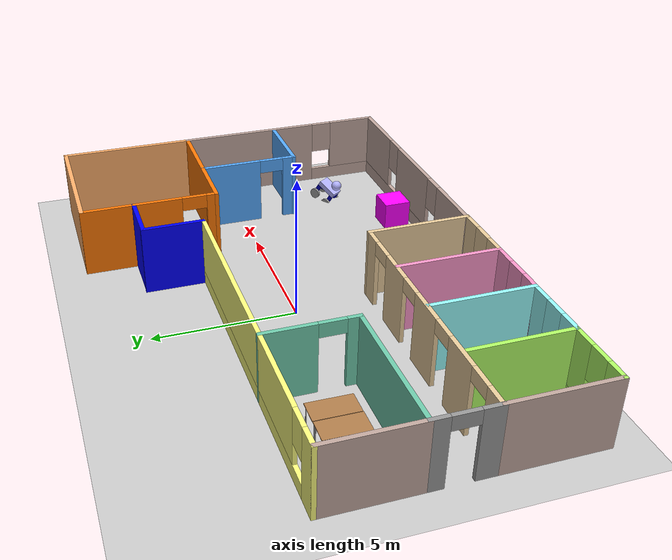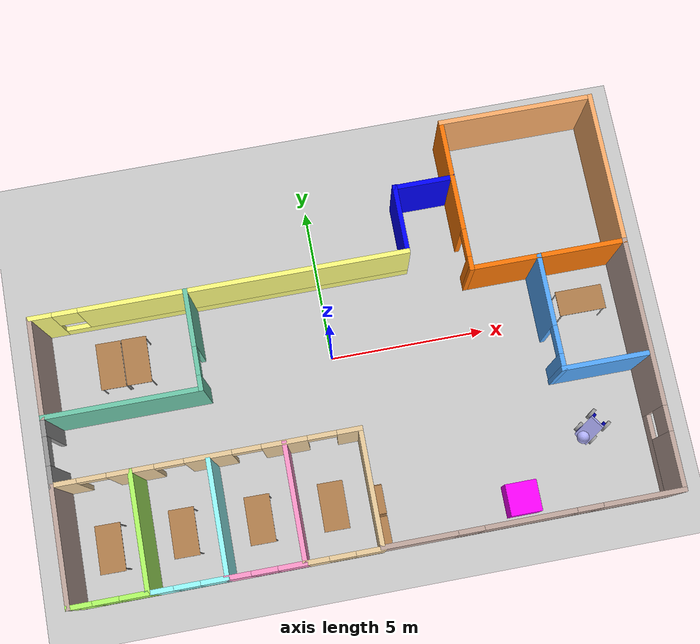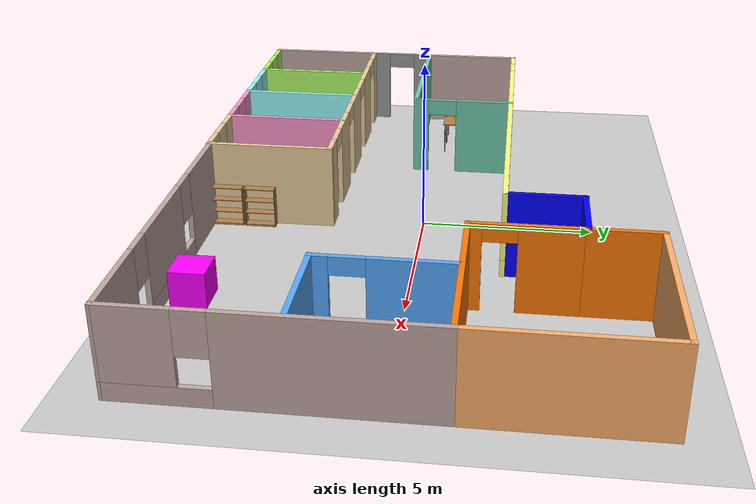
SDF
<sdf version="1.6">
 <world name="default">
  <plugin name="welcome" filename="libwelcome.so"/>
  <light name="sun" type="directional">
   <pose>0 0 10 0 -0 0</pose>
   <diffuse>0.8 0.8 0.8 1</diffuse>
   <specular>0.1 0.1 0.1 1</specular>
   <attenuation>
    <range>1000</range>
    <constant>0.9</constant>
    <linear>0.01</linear>
    <quadratic>0.001</quadratic>
   </attenuation>
   <direction>-0.5 0.5 -1</direction>
  </light>
  <model name="ground_plane">
   <static>1</static>
   <link name="link">
    <collision name="collision">
     <geometry><plane><normal>0 0 1</normal><size>100 100</size></plane></geometry>
     <surface><friction><ode><mu>100</mu><mu2>50</mu2></ode></friction></surface>
    </collision>
    <visual name="visual">
     <cast_shadows>0</cast_shadows>
     <geometry><plane><normal>0 0 1</normal><size>100 100</size></plane></geometry>
     <material>
      <script><uri>file://media/materials/scripts/gazebo.material</uri><name>Gazebo/Grey</name></script>
     </material>
    </visual>
   </link>
  </model>
  <gravity>0 0 -9.8</gravity>
  <magnetic_field>6e-06 2.3e-05 -4.2e-05</magnetic_field>
  <atmosphere type="adiabatic"/>
  <physics name="default_physics" default="0" type="ode">
   <max_step_size>0.001</max_step_size>
   <real_time_factor>1</real_time_factor>
   <real_time_update_rate>1000</real_time_update_rate>
  </physics>
  <scene><ambient>0.4 0.4 0.4 1</ambient><background>0.7 0.7 0.7 1</background><shadows>1</shadows></scene>
  <spherical_coordinates>
   <surface_model>EARTH_WGS84</surface_model>
   <latitude_deg>0</latitude_deg>
   <longitude_deg>0</longitude_deg>
   <elevation>0</elevation>
   <heading_deg>0</heading_deg>
  </spherical_coordinates>
  <model name="Building">
   <pose>0.30391 0.642742 0 0 -0 0</pose>
   <link name="Wall_0">
    <collision name="Wall_0_Collision">
     <geometry><box><size>5 0.15 2.5</size></box></geometry>
     <pose>0 0 1.25 0 -0 0</pose>
    </collision>
    <visual name="Wall_0_Visual">
     <pose>0 0 1.25 0 -0 0</pose>
     <geometry><box><size>5 0.15 2.5</size></box></geometry>
     <material>
      <script><uri>file://media/materials/scripts/gazebo.material</uri><name>Gazebo/Grey</name></script>
      <ambient>0.435294 0.796078 0.67451 1</ambient>
     </material>
     <meta><layer>0</layer></meta>
    </visual>
    <pose>-6.85008 -1.3 0 0 -0 0</pose>
   </link>
   <link name="Wall_1">
    <pose>-4.42508 0.25 0 0 -0 1.5708</pose>
    <visual name="Wall_1_Visual_0">
     <pose>-1.37584 0 1.25 0 -0 0</pose>
     <geometry><box><size>0.498315 0.15 2.5</size></box></geometry>
     <material>
      <script><uri>file://media/materials/scripts/gazebo.material</uri><name>Gazebo/Grey</name></script>
      <ambient>0.435294 0.796078 0.67451 1</ambient>
     </material>
     <meta><layer>0</layer></meta>
    </visual>
    <collision name="Wall_1_Collision_0">
     <geometry><box><size>0.498315 0.15 2.5</size></box></geometry>
     <pose>-1.37584 0 1.25 0 -0 0</pose>
    </collision>
    <visual name="Wall_1_Visual_1">
     <pose>0.699158 0 1.25 0 -0 0</pose>
     <geometry><box><size>1.85169 0.15 2.5</size></box></geometry>
     <material>
      <script><uri>file://media/materials/scripts/gazebo.material</uri><name>Gazebo/Grey</name></script>
      <ambient>0.435294 0.796078 0.67451 1</ambient>
     </material>
     <meta><layer>0</layer></meta>
    </visual>
    <collision name="Wall_1_Collision_1">
     <geometry><box><size>1.85169 0.15 2.5</size></box></geometry>
     <pose>0.699158 0 1.25 0 -0 0</pose>
    </collision>
    <visual name="Wall_1_Visual_2">
     <pose>-0.676685 0 2.25 0 -0 0</pose>
     <geometry><box><size>0.9 0.15 0.5</size></box></geometry>
     <material>
      <script><uri>file://media/materials/scripts/gazebo.material</uri><name>Gazebo/Grey</name></script>
      <ambient>0.435294 0.796078 0.67451 1</ambient>
     </material>
     <meta><layer>0</layer></meta>
    </visual>
    <collision name="Wall_1_Collision_2">
     <geometry><box><size>0.9 0.15 0.5</size></box></geometry>
     <pose>-0.676685 0 2.25 0 -0 0</pose>
    </collision>
   </link>
   <link name="Wall_10">
    <pose>-3.40008 -7 0 0 -0 0</pose>
    <visual name="Wall_10_Visual_0">
     <pose>-0.845921 0 1.25 0 -0 0</pose>
     <geometry><box><size>0.808158 0.15 2.5</size></box></geometry>
     <material>
      <script><uri>file://media/materials/scripts/gazebo.material</uri><name>Gazebo/Grey</name></script>
      <ambient>1 0.6 0.8 1</ambient>
     </material>
     <meta><layer>0</layer></meta>
    </visual>
    <collision name="Wall_10_Collision_0">
     <geometry><box><size>0.808158 0.15 2.5</size></box></geometry>
     <pose>-0.845921 0 1.25 0 -0 0</pose>
    </collision>
    <visual name="Wall_10_Visual_1">
     <pose>0.404079 0 0.25 0 -0 0</pose>
     <geometry><box><size>1.69184 0.15 0.5</size></box></geometry>
     <material>
      <script><uri>file://media/materials/scripts/gazebo.material</uri><name>Gazebo/Grey</name></script>
      <ambient>1 0.6 0.8 1</ambient>
     </material>
     <meta><layer>0</layer></meta>
    </visual>
    <collision name="Wall_10_Collision_1">
     <geometry><box><size>1.69184 0.15 0.5</size></box></geometry>
     <pose>0.404079 0 0.25 0 -0 0</pose>
    </collision>
    <visual name="Wall_10_Visual_2">
     <pose>0.804079 0 1.5 0 -0 0</pose>
     <geometry><box><size>0.891842 0.15 2</size></box></geometry>
     <material>
      <script><uri>file://media/materials/scripts/gazebo.material</uri><name>Gazebo/Grey</name></script>
      <ambient>1 0.6 0.8 1</ambient>
     </material>
     <meta><layer>0</layer></meta>
    </visual>
    <collision name="Wall_10_Collision_2">
     <geometry><box><size>0.891842 0.15 2</size></box></geometry>
     <pose>0.804079 0 1.5 0 -0 0</pose>
    </collision>
    <visual name="Wall_10_Visual_3">
     <pose>-0.041842 0 1.9 0 -0 0</pose>
     <geometry><box><size>0.8 0.15 1.2</size></box></geometry>
     <material>
      <script><uri>file://media/materials/scripts/gazebo.material</uri><name>Gazebo/Grey</name></script>
      <ambient>1 0.6 0.8 1</ambient>
     </material>
     <meta><layer>0</layer></meta>
    </visual>
    <collision name="Wall_10_Collision_3">
     <geometry><box><size>0.8 0.15 1.2</size></box></geometry>
     <pose>-0.041842 0 1.9 0 -0 0</pose>
    </collision>
   </link>
   <link name="Wall_11">
    <pose>-1.05008 -7 0 0 -0 0</pose>
    <visual name="Wall_11_Visual_0">
     <pose>-0.851227 0 1.25 0 -0 0</pose>
     <geometry><box><size>0.797546 0.15 2.5</size></box></geometry>
     <material>
      <script><uri>file://media/materials/scripts/gazebo.material</uri><name>Gazebo/Grey</name></script>
      <ambient>0.921569 0.807843 0.615686 1</ambient>
     </material>
     <meta><layer>0</layer></meta>
    </visual>
    <collision name="Wall_11_Collision_0">
     <geometry><box><size>0.797546 0.15 2.5</size></box></geometry>
     <pose>-0.851227 0 1.25 0 -0 0</pose>
    </collision>
    <visual name="Wall_11_Visual_1">
     <pose>0.398773 0 0.25 0 -0 0</pose>
     <geometry><box><size>1.70245 0.15 0.5</size></box></geometry>
     <material>
      <script><uri>file://media/materials/scripts/gazebo.material</uri><name>Gazebo/Grey</name></script>
      <ambient>0.921569 0.807843 0.615686 1</ambient>
     </material>
     <meta><layer>0</layer></meta>
    </visual>
    <collision name="Wall_11_Collision_1">
     <geometry><box><size>1.70245 0.15 0.5</size></box></geometry>
     <pose>0.398773 0 0.25 0 -0 0</pose>
    </collision>
    <visual name="Wall_11_Visual_2">
     <pose>0.798773 0 1.5 0 -0 0</pose>
     <geometry><box><size>0.902454 0.15 2</size></box></geometry>
     <material>
      <script><uri>file://media/materials/scripts/gazebo.material</uri><name>Gazebo/Grey</name></script>
      <ambient>0.921569 0.807843 0.615686 1</ambient>
     </material>
     <meta><layer>0</layer></meta>
    </visual>
    <collision name="Wall_11_Collision_2">
     <geometry><box><size>0.902454 0.15 2</size></box></geometry>
     <pose>0.798773 0 1.5 0 -0 0</pose>
    </collision>
    <visual name="Wall_11_Visual_3">
     <pose>-0.052454 0 1.9 0 -0 0</pose>
     <geometry><box><size>0.8 0.15 1.2</size></box></geometry>
     <material>
      <script><uri>file://media/materials/scripts/gazebo.material</uri><name>Gazebo/Grey</name></script>
      <ambient>0.921569 0.807843 0.615686 1</ambient>
     </material>
     <meta><layer>0</layer></meta>
    </visual>
    <collision name="Wall_11_Collision_3">
     <geometry><box><size>0.8 0.15 1.2</size></box></geometry>
     <pose>-0.052454 0 1.9 0 -0 0</pose>
    </collision>
   </link>
   <link name="Wall_13">
    <collision name="Wall_13_Collision">
     <geometry><box><size>3.75 0.15 2.5</size></box></geometry>
     <pose>0 0 1.25 0 -0 0</pose>
    </collision>
    <visual name="Wall_13_Visual">
     <pose>0 0 1.25 0 -0 0</pose>
     <geometry><box><size>3.75 0.15 2.5</size></box></geometry>
     <material>
      <script><uri>file://media/materials/scripts/gazebo.material</uri><name>Gazebo/Grey</name></script>
      <ambient>0.7 1 0.4 1</ambient>
     </material>
     <meta><layer>0</layer></meta>
    </visual>
    <pose>-6.90893 -5.18287 0 0 0 -1.5708</pose>
   </link>
   <link name="Wall_15">
    <collision name="Wall_15_Collision">
     <geometry><box><size>3.75 0.15 2.5</size></box></geometry>
     <pose>0 0 1.25 0 -0 0</pose>
    </collision>
    <visual name="Wall_15_Visual">
     <pose>0 0 1.25 0 -0 0</pose>
     <geometry><box><size>3.75 0.15 2.5</size></box></geometry>
     <material>
      <script><uri>file://media/materials/scripts/gazebo.material</uri><name>Gazebo/Grey</name></script>
      <ambient>0.6 1 1 1</ambient>
     </material>
     <meta><layer>0</layer></meta>
    </visual>
    <pose>-4.55349 -5.19817 0 0 0 -1.5708</pose>
   </link>
   <link name="Wall_20">
    <collision name="Wall_20_Collision">
     <geometry><box><size>3.75 0.15 2.5</size></box></geometry>
     <pose>0 0 1.25 0 -0 0</pose>
    </collision>
    <visual name="Wall_20_Visual">
     <pose>0 0 1.25 0 -0 0</pose>
     <geometry><box><size>3.75 0.15 2.5</size></box></geometry>
     <material>
      <script><uri>file://media/materials/scripts/gazebo.material</uri><name>Gazebo/Grey</name></script>
      <ambient>0.921569 0.807843 0.615686 1</ambient>
     </material>
     <meta><layer>0</layer></meta>
    </visual>
    <pose>0.105511 -5.16941 0 0 0 -1.5708</pose>
   </link>
   <link name="Wall_22">
    <pose>-4.56949 -3.36941 0 0 -0 3.14159</pose>
    <visual name="Wall_22_Visual_0">
     <pose>-4.35107 0 1.25 0 -0 0</pose>
     <geometry><box><size>0.797866 0.15 2.5</size></box></geometry>
     <material>
      <script><uri>file://media/materials/scripts/gazebo.material</uri><name>Gazebo/Grey</name></script>
      <ambient>0.921569 0.807843 0.615686 1</ambient>
     </material>
     <meta><layer>0</layer></meta>
    </visual>
    <collision name="Wall_22_Collision_0">
     <geometry><box><size>0.797866 0.15 2.5</size></box></geometry>
     <pose>-4.35107 0 1.25 0 -0 0</pose>
    </collision>
    <visual name="Wall_22_Visual_1">
     <pose>-2.35003 0 1.25 0 -0 0</pose>
     <geometry><box><size>1.40421 0.15 2.5</size></box></geometry>
     <material>
      <script><uri>file://media/materials/scripts/gazebo.material</uri><name>Gazebo/Grey</name></script>
      <ambient>0.921569 0.807843 0.615686 1</ambient>
     </material>
     <meta><layer>0</layer></meta>
    </visual>
    <collision name="Wall_22_Collision_1">
     <geometry><box><size>1.40421 0.15 2.5</size></box></geometry>
     <pose>-2.35003 0 1.25 0 -0 0</pose>
    </collision>
    <visual name="Wall_22_Visual_2">
     <pose>-0.019437 0 1.25 0 -0 0</pose>
     <geometry><box><size>1.45698 0.15 2.5</size></box></geometry>
     <material>
      <script><uri>file://media/materials/scripts/gazebo.material</uri><name>Gazebo/Grey</name></script>
      <ambient>0.921569 0.807843 0.615686 1</ambient>
     </material>
     <meta><layer>0</layer></meta>
    </visual>
    <collision name="Wall_22_Collision_2">
     <geometry><box><size>1.45698 0.15 2.5</size></box></geometry>
     <pose>-0.019437 0 1.25 0 -0 0</pose>
    </collision>
    <visual name="Wall_22_Visual_3">
     <pose>2.32875 0 1.25 0 -0 0</pose>
     <geometry><box><size>1.43939 0.15 2.5</size></box></geometry>
     <material>
      <script><uri>file://media/materials/scripts/gazebo.material</uri><name>Gazebo/Grey</name></script>
      <ambient>0.921569 0.807843 0.615686 1</ambient>
     </material>
     <meta><layer>0</layer></meta>
    </visual>
    <collision name="Wall_22_Collision_3">
     <geometry><box><size>1.43939 0.15 2.5</size></box></geometry>
     <pose>2.32875 0 1.25 0 -0 0</pose>
    </collision>
    <visual name="Wall_22_Visual_4">
     <pose>4.34922 0 1.25 0 -0 0</pose>
     <geometry><box><size>0.801561 0.15 2.5</size></box></geometry>
     <material>
      <script><uri>file://media/materials/scripts/gazebo.material</uri><name>Gazebo/Grey</name></script>
      <ambient>0.921569 0.807843 0.615686 1</ambient>
     </material>
     <meta><layer>0</layer></meta>
    </visual>
    <collision name="Wall_22_Collision_4">
     <geometry><box><size>0.801561 0.15 2.5</size></box></geometry>
     <pose>4.34922 0 1.25 0 -0 0</pose>
    </collision>
    <visual name="Wall_22_Visual_5">
     <pose>-3.50213 0 2.25 0 -0 0</pose>
     <geometry><box><size>0.9 0.15 0.5</size></box></geometry>
     <material>
      <script><uri>file://media/materials/scripts/gazebo.material</uri><name>Gazebo/Grey</name></script>
      <ambient>0.921569 0.807843 0.615686 1</ambient>
     </material>
     <meta><layer>0</layer></meta>
    </visual>
    <collision name="Wall_22_Collision_5">
     <geometry><box><size>0.9 0.15 0.5</size></box></geometry>
     <pose>-3.50213 0 2.25 0 -0 0</pose>
    </collision>
    <visual name="Wall_22_Visual_6">
     <pose>-1.19792 0 2.25 0 -0 0</pose>
     <geometry><box><size>0.9 0.15 0.5</size></box></geometry>
     <material>
      <script><uri>file://media/materials/scripts/gazebo.material</uri><name>Gazebo/Grey</name></script>
      <ambient>0.921569 0.807843 0.615686 1</ambient>
     </material>
     <meta><layer>0</layer></meta>
    </visual>
    <collision name="Wall_22_Collision_6">
     <geometry><box><size>0.9 0.15 0.5</size></box></geometry>
     <pose>-1.19792 0 2.25 0 -0 0</pose>
    </collision>
    <visual name="Wall_22_Visual_7">
     <pose>1.15905 0 2.25 0 -0 0</pose>
     <geometry><box><size>0.9 0.15 0.5</size></box></geometry>
     <material>
      <script><uri>file://media/materials/scripts/gazebo.material</uri><name>Gazebo/Grey</name></script>
      <ambient>0.921569 0.807843 0.615686 1</ambient>
     </material>
     <meta><layer>0</layer></meta>
    </visual>
    <collision name="Wall_22_Collision_7">
     <geometry><box><size>0.9 0.15 0.5</size></box></geometry>
     <pose>1.15905 0 2.25 0 -0 0</pose>
    </collision>
    <visual name="Wall_22_Visual_8">
     <pose>3.49844 0 2.25 0 -0 0</pose>
     <geometry><box><size>0.9 0.15 0.5</size></box></geometry>
     <material>
      <script><uri>file://media/materials/scripts/gazebo.material</uri><name>Gazebo/Grey</name></script>
      <ambient>0.921569 0.807843 0.615686 1</ambient>
     </material>
     <meta><layer>0</layer></meta>
    </visual>
    <collision name="Wall_22_Collision_8">
     <geometry><box><size>0.9 0.15 0.5</size></box></geometry>
     <pose>3.49844 0 2.25 0 -0 0</pose>
    </collision>
   </link>
   <link name="Wall_24">
    <collision name="Wall_24_Collision">
     <geometry><box><size>3.75 0.15 2.5</size></box></geometry>
     <pose>0 0 1.25 0 -0 0</pose>
    </collision>
    <visual name="Wall_24_Visual">
     <pose>0 0 1.25 0 -0 0</pose>
     <geometry><box><size>3.75 0.15 2.5</size></box></geometry>
     <material>
      <script><uri>file://media/materials/scripts/gazebo.material</uri><name>Gazebo/Grey</name></script>
      <ambient>1 0.6 0.8 1</ambient>
     </material>
     <meta><layer>0</layer></meta>
    </visual>
    <pose>-2.22508 -5.2 0 0 -0 1.5708</pose>
   </link>
   <link name="Wall_27">
    <pose>-3.35008 1.8 0 0 -0 0</pose>
    <visual name="Wall_27_Visual_0">
     <pose>-5.61169 0 1.25 0 -0 0</pose>
     <geometry><box><size>0.776615 0.15 2.5</size></box></geometry>
     <material>
      <script><uri>file://media/materials/scripts/gazebo.material</uri><name>Gazebo/Grey</name></script>
      <ambient>1 1 0.498039 1</ambient>
     </material>
     <meta><layer>0</layer></meta>
    </visual>
    <collision name="Wall_27_Collision_0">
     <geometry><box><size>0.776615 0.15 2.5</size></box></geometry>
     <pose>-5.61169 0 1.25 0 -0 0</pose>
    </collision>
    <visual name="Wall_27_Visual_1">
     <pose>0.388307 0 0.25 0 -0 0</pose>
     <geometry><box><size>11.2234 0.15 0.5</size></box></geometry>
     <material>
      <script><uri>file://media/materials/scripts/gazebo.material</uri><name>Gazebo/Grey</name></script>
      <ambient>1 1 0.498039 1</ambient>
     </material>
     <meta><layer>0</layer></meta>
    </visual>
    <collision name="Wall_27_Collision_1">
     <geometry><box><size>11.2234 0.15 0.5</size></box></geometry>
     <pose>0.388307 0 0.25 0 -0 0</pose>
    </collision>
    <visual name="Wall_27_Visual_2">
     <pose>0.788307 0 1.5 0 -0 0</pose>
     <geometry><box><size>10.4234 0.15 2</size></box></geometry>
     <material>
      <script><uri>file://media/materials/scripts/gazebo.material</uri><name>Gazebo/Grey</name></script>
      <ambient>1 1 0.498039 1</ambient>
     </material>
     <meta><layer>0</layer></meta>
    </visual>
    <collision name="Wall_27_Collision_2">
     <geometry><box><size>10.4234 0.15 2</size></box></geometry>
     <pose>0.788307 0 1.5 0 -0 0</pose>
    </collision>
    <visual name="Wall_27_Visual_3">
     <pose>-4.82339 0 1.9 0 -0 0</pose>
     <geometry><box><size>0.8 0.15 1.2</size></box></geometry>
     <material>
      <script><uri>file://media/materials/scripts/gazebo.material</uri><name>Gazebo/Grey</name></script>
      <ambient>1 1 0.498039 1</ambient>
     </material>
     <meta><layer>0</layer></meta>
    </visual>
    <collision name="Wall_27_Collision_3">
     <geometry><box><size>0.8 0.15 1.2</size></box></geometry>
     <pose>-4.82339 0 1.9 0 -0 0</pose>
    </collision>
   </link>
   <link name="Wall_29">
    <pose>2.57492 2.85 0 0 -0 1.5708</pose>
    <visual name="Wall_29_Visual">
     <pose>0.01253 0 1.25 0 -0 0</pose>
     <geometry><box><size>2.25 0.15 2.5</size></box></geometry>
     <material>
      <script><uri>file://media/materials/scripts/gazebo.material</uri><name>Gazebo/Grey</name></script>
      <ambient>0 0 1 1</ambient>
     </material>
     <meta><layer>0</layer></meta>
    </visual>
    <collision name="Wall_29_Collision">
     <geometry><box><size>2.25 0.15 2.5</size></box></geometry>
     <pose>0.01253 0 1.25 0 -0 0</pose>
    </collision>
   </link>
   <link name="Wall_3">
    <collision name="Wall_3_Collision">
     <geometry><box><size>3.25 0.15 2.5</size></box></geometry>
     <pose>0 0 1.25 0 -0 0</pose>
    </collision>
    <visual name="Wall_3_Visual">
     <pose>0 0 1.25 0 -0 0</pose>
     <geometry><box><size>3.25 0.15 2.5</size></box></geometry>
     <material>
      <script><uri>file://media/materials/scripts/gazebo.material</uri><name>Gazebo/Grey</name></script>
      <ambient>0.760784 0.662745 0.627451 1</ambient>
     </material>
     <meta><layer>0</layer></meta>
    </visual>
    <pose>-9.27508 0.25 0 0 0 -1.5708</pose>
   </link>
   <link name="Wall_39">
    <collision name="Wall_39_Collision">
     <geometry><box><size>2 0.15 2.5</size></box></geometry>
     <pose>0 0 1.25 0 -0 0</pose>
    </collision>
    <visual name="Wall_39_Visual">
     <pose>0 0 1.25 0 -0 0</pose>
     <geometry><box><size>2 0.15 2.5</size></box></geometry>
     <material>
      <script><uri>file://media/materials/scripts/gazebo.material</uri><name>Gazebo/Grey</name></script>
      <ambient>0 0 1 1</ambient>
     </material>
     <meta><layer>0</layer></meta>
    </visual>
    <pose>3.49992 3.9 0 0 -0 0</pose>
   </link>
   <link name="Wall_40">
    <collision name="Wall_40_Collision">
     <geometry><box><size>2 0.15 2.5</size></box></geometry>
     <pose>0 0 1.25 0 -0 0</pose>
    </collision>
    <visual name="Wall_40_Visual">
     <pose>0 0 1.25 0 -0 0</pose>
     <geometry><box><size>2 0.15 2.5</size></box></geometry>
     <material>
      <script><uri>file://media/materials/scripts/gazebo.material</uri><name>Gazebo/Grey</name></script>
      <ambient>0.996078 0.47451 0.0196078 1</ambient>
     </material>
     <meta><layer>0</layer></meta>
    </visual>
    <pose>4.42492 4.825 0 0 -0 1.5708</pose>
   </link>
   <link name="Wall_42">
    <collision name="Wall_42_Collision">
     <geometry><box><size>5 0.15 2.5</size></box></geometry>
     <pose>0 0 1.25 0 -0 0</pose>
    </collision>
    <visual name="Wall_42_Visual">
     <pose>0 0 1.25 0 -0 0</pose>
     <geometry><box><size>5 0.15 2.5</size></box></geometry>
     <material>
      <script><uri>file://media/materials/scripts/gazebo.material</uri><name>Gazebo/Grey</name></script>
      <ambient>1 0.69 0.42 1</ambient>
     </material>
     <meta><layer>0</layer></meta>
    </visual>
    <pose>6.84992 5.75 0 0 -0 0</pose>
   </link>
   <link name="Wall_47">
    <collision name="Wall_47_Collision">
     <geometry><box><size>5 0.15 2.5</size></box></geometry>
     <pose>0 0 1.25 0 -0 0</pose>
    </collision>
    <visual name="Wall_47_Visual">
     <pose>0 0 1.25 0 -0 0</pose>
     <geometry><box><size>5 0.15 2.5</size></box></geometry>
     <material>
      <script><uri>file://media/materials/scripts/gazebo.material</uri><name>Gazebo/Grey</name></script>
      <ambient>1 0.69 0.42 1</ambient>
     </material>
     <meta><layer>0</layer></meta>
    </visual>
    <pose>9.27492 3.325 0 0 0 -1.5708</pose>
   </link>
   <link name="Wall_48">
    <collision name="Wall_48_Collision">
     <geometry><box><size>5 0.15 2.5</size></box></geometry>
     <pose>0 0 1.25 0 -0 0</pose>
    </collision>
    <visual name="Wall_48_Visual">
     <pose>0 0 1.25 0 -0 0</pose>
     <geometry><box><size>5 0.15 2.5</size></box></geometry>
     <material>
      <script><uri>file://media/materials/scripts/gazebo.material</uri><name>Gazebo/Grey</name></script>
      <ambient>0.996078 0.47451 0.0196078 1</ambient>
     </material>
     <meta><layer>0</layer></meta>
    </visual>
    <pose>6.84992 0.9 0 0 -0 3.14159</pose>
   </link>
   <link name="Wall_5">
    <pose>-9.27508 -2.35 0 0 0 -1.5708</pose>
    <visual name="Wall_5_Visual_0">
     <pose>-0.799331 0 1.25 0 -0 0</pose>
     <geometry><box><size>0.651337 0.15 2.5</size></box></geometry>
     <material>
      <script><uri>file://media/materials/scripts/gazebo.material</uri><name>Gazebo/Grey</name></script>
      <ambient>1 1 1 1</ambient>
     </material>
     <meta><layer>0</layer></meta>
    </visual>
    <collision name="Wall_5_Collision_0">
     <geometry><box><size>0.651337 0.15 2.5</size></box></geometry>
     <pose>-0.799331 0 1.25 0 -0 0</pose>
    </collision>
    <visual name="Wall_5_Visual_1">
     <pose>0.775669 0 1.25 0 -0 0</pose>
     <geometry><box><size>0.698663 0.15 2.5</size></box></geometry>
     <material>
      <script><uri>file://media/materials/scripts/gazebo.material</uri><name>Gazebo/Grey</name></script>
      <ambient>1 1 1 1</ambient>
     </material>
     <meta><layer>0</layer></meta>
    </visual>
    <collision name="Wall_5_Collision_1">
     <geometry><box><size>0.698663 0.15 2.5</size></box></geometry>
     <pose>0.775669 0 1.25 0 -0 0</pose>
    </collision>
    <visual name="Wall_5_Visual_2">
     <pose>-0.023663 0 2.25 0 -0 0</pose>
     <geometry><box><size>0.9 0.15 0.5</size></box></geometry>
     <material>
      <script><uri>file://media/materials/scripts/gazebo.material</uri><name>Gazebo/Grey</name></script>
      <ambient>1 1 1 1</ambient>
     </material>
     <meta><layer>0</layer></meta>
    </visual>
    <collision name="Wall_5_Collision_2">
     <geometry><box><size>0.9 0.15 0.5</size></box></geometry>
     <pose>-0.023663 0 2.25 0 -0 0</pose>
    </collision>
   </link>
   <link name="Wall_50">
    <pose>4.42492 2.4 0 0 -0 1.5708</pose>
    <visual name="Wall_50_Visual_0">
     <pose>-1.35289 0 1.25 0 -0 0</pose>
     <geometry><box><size>0.44422 0.15 2.5</size></box></geometry>
     <material>
      <script><uri>file://media/materials/scripts/gazebo.material</uri><name>Gazebo/Grey</name></script>
      <ambient>0.996078 0.47451 0.0196078 1</ambient>
     </material>
     <meta><layer>0</layer></meta>
    </visual>
    <collision name="Wall_50_Collision_0">
     <geometry><box><size>0.44422 0.15 2.5</size></box></geometry>
     <pose>-1.35289 0 1.25 0 -0 0</pose>
    </collision>
    <visual name="Wall_50_Visual_1">
     <pose>0.67211 0 1.25 0 -0 0</pose>
     <geometry><box><size>1.80578 0.15 2.5</size></box></geometry>
     <material>
      <script><uri>file://media/materials/scripts/gazebo.material</uri><name>Gazebo/Grey</name></script>
      <ambient>0.996078 0.47451 0.0196078 1</ambient>
     </material>
     <meta><layer>0</layer></meta>
    </visual>
    <collision name="Wall_50_Collision_1">
     <geometry><box><size>1.80578 0.15 2.5</size></box></geometry>
     <pose>0.67211 0 1.25 0 -0 0</pose>
    </collision>
    <visual name="Wall_50_Visual_2">
     <pose>-0.68078 0 2.25 0 -0 0</pose>
     <geometry><box><size>0.9 0.15 0.5</size></box></geometry>
     <material>
      <script><uri>file://media/materials/scripts/gazebo.material</uri><name>Gazebo/Grey</name></script>
      <ambient>0.996078 0.47451 0.0196078 1</ambient>
     </material>
     <meta><layer>0</layer></meta>
    </visual>
    <collision name="Wall_50_Collision_2">
     <geometry><box><size>0.9 0.15 0.5</size></box></geometry>
     <pose>-0.68078 0 2.25 0 -0 0</pose>
    </collision>
   </link>
   <link name="Wall_52">
    <pose>9.27492 -3.025 0 0 0 -1.5708</pose>
    <visual name="Wall_52_Visual_0">
     <pose>-1.32687 0 1.25 0 -0 0</pose>
     <geometry><box><size>5.34626 0.15 2.5</size></box></geometry>
     <material>
      <script><uri>file://media/materials/scripts/gazebo.material</uri><name>Gazebo/Grey</name></script>
      <ambient>0.760784 0.662745 0.627451 1</ambient>
     </material>
     <meta><layer>0</layer></meta>
    </visual>
    <collision name="Wall_52_Collision_0">
     <geometry><box><size>5.34626 0.15 2.5</size></box></geometry>
     <pose>-1.32687 0 1.25 0 -0 0</pose>
    </collision>
    <visual name="Wall_52_Visual_1">
     <pose>2.67313 0 0.25 0 -0 0</pose>
     <geometry><box><size>2.65374 0.15 0.5</size></box></geometry>
     <material>
      <script><uri>file://media/materials/scripts/gazebo.material</uri><name>Gazebo/Grey</name></script>
      <ambient>0.760784 0.662745 0.627451 1</ambient>
     </material>
     <meta><layer>0</layer></meta>
    </visual>
    <collision name="Wall_52_Collision_1">
     <geometry><box><size>2.65374 0.15 0.5</size></box></geometry>
     <pose>2.67313 0 0.25 0 -0 0</pose>
    </collision>
    <visual name="Wall_52_Visual_2">
     <pose>3.07313 0 1.5 0 -0 0</pose>
     <geometry><box><size>1.85374 0.15 2</size></box></geometry>
     <material>
      <script><uri>file://media/materials/scripts/gazebo.material</uri><name>Gazebo/Grey</name></script>
      <ambient>0.760784 0.662745 0.627451 1</ambient>
     </material>
     <meta><layer>0</layer></meta>
    </visual>
    <collision name="Wall_52_Collision_2">
     <geometry><box><size>1.85374 0.15 2</size></box></geometry>
     <pose>3.07313 0 1.5 0 -0 0</pose>
    </collision>
    <visual name="Wall_52_Visual_3">
     <pose>1.74626 0 1.9 0 -0 0</pose>
     <geometry><box><size>0.8 0.15 1.2</size></box></geometry>
     <material>
      <script><uri>file://media/materials/scripts/gazebo.material</uri><name>Gazebo/Grey</name></script>
      <ambient>0.760784 0.662745 0.627451 1</ambient>
     </material>
     <meta><layer>0</layer></meta>
    </visual>
    <collision name="Wall_52_Collision_3">
     <geometry><box><size>0.8 0.15 1.2</size></box></geometry>
     <pose>1.74626 0 1.9 0 -0 0</pose>
    </collision>
   </link>
   <link name="Wall_56">
    <pose>4.69022 -6.9597 0 0 -0 0.002117</pose>
    <visual name="Wall_56_Visual_0">
     <pose>-3.48265 0 1.25 0 -0 0</pose>
     <geometry><box><size>2.35413 0.15 2.5</size></box></geometry>
     <material>
      <script><uri>file://media/materials/scripts/gazebo.material</uri><name>Gazebo/Grey</name></script>
      <ambient>0.760784 0.662745 0.627451 1</ambient>
     </material>
     <meta><layer>0</layer></meta>
    </visual>
    <collision name="Wall_56_Collision_0">
     <geometry><box><size>2.35413 0.15 2.5</size></box></geometry>
     <pose>-3.48265 0 1.25 0 -0 0</pose>
    </collision>
    <visual name="Wall_56_Visual_1">
     <pose>1.17706 0 0.25 0 -0 0</pose>
     <geometry><box><size>6.9653 0.15 0.5</size></box></geometry>
     <material>
      <script><uri>file://media/materials/scripts/gazebo.material</uri><name>Gazebo/Grey</name></script>
      <ambient>0.760784 0.662745 0.627451 1</ambient>
     </material>
     <meta><layer>0</layer></meta>
    </visual>
    <collision name="Wall_56_Collision_1">
     <geometry><box><size>6.9653 0.15 0.5</size></box></geometry>
     <pose>1.17706 0 0.25 0 -0 0</pose>
    </collision>
    <visual name="Wall_56_Visual_2">
     <pose>-0.102624 0 1.5 0 -0 0</pose>
     <geometry><box><size>2.80593 0.15 2</size></box></geometry>
     <material>
      <script><uri>file://media/materials/scripts/gazebo.material</uri><name>Gazebo/Grey</name></script>
      <ambient>0.760784 0.662745 0.627451 1</ambient>
     </material>
     <meta><layer>0</layer></meta>
    </visual>
    <collision name="Wall_56_Collision_2">
     <geometry><box><size>2.80593 0.15 2</size></box></geometry>
     <pose>-0.102624 0 1.5 0 -0 0</pose>
    </collision>
    <visual name="Wall_56_Visual_3">
     <pose>3.38003 0 1.5 0 -0 0</pose>
     <geometry><box><size>2.55938 0.15 2</size></box></geometry>
     <material>
      <script><uri>file://media/materials/scripts/gazebo.material</uri><name>Gazebo/Grey</name></script>
      <ambient>0.760784 0.662745 0.627451 1</ambient>
     </material>
     <meta><layer>0</layer></meta>
    </visual>
    <collision name="Wall_56_Collision_3">
     <geometry><box><size>2.55938 0.15 2</size></box></geometry>
     <pose>3.38003 0 1.5 0 -0 0</pose>
    </collision>
    <visual name="Wall_56_Visual_4">
     <pose>-1.90559 0 1.9 0 -0 0</pose>
     <geometry><box><size>0.8 0.15 1.2</size></box></geometry>
     <material>
      <script><uri>file://media/materials/scripts/gazebo.material</uri><name>Gazebo/Grey</name></script>
      <ambient>0.760784 0.662745 0.627451 1</ambient>
     </material>
     <meta><layer>0</layer></meta>
    </visual>
    <collision name="Wall_56_Collision_4">
     <geometry><box><size>0.8 0.15 1.2</size></box></geometry>
     <pose>-1.90559 0 1.9 0 -0 0</pose>
    </collision>
    <visual name="Wall_56_Visual_5">
     <pose>1.70034 0 1.9 0 -0 0</pose>
     <geometry><box><size>0.8 0.15 1.2</size></box></geometry>
     <material>
      <script><uri>file://media/materials/scripts/gazebo.material</uri><name>Gazebo/Grey</name></script>
      <ambient>0.760784 0.662745 0.627451 1</ambient>
     </material>
     <meta><layer>0</layer></meta>
    </visual>
    <collision name="Wall_56_Collision_5">
     <geometry><box><size>0.8 0.15 1.2</size></box></geometry>
     <pose>1.70034 0 1.9 0 -0 0</pose>
    </collision>
   </link>
   <link name="Wall_58">
    <pose>6.54885 -0.907481 0 0 0 -1.5708</pose>
    <visual name="Wall_58_Visual_0">
     <pose>-0.716912 0 1.25 0 -0 0</pose>
     <geometry><box><size>2.31617 0.15 2.5</size></box></geometry>
     <material>
      <script><uri>file://media/materials/scripts/gazebo.material</uri><name>Gazebo/Grey</name></script>
      <ambient>0.333333 0.666667 1 1</ambient>
     </material>
     <meta><layer>0</layer></meta>
    </visual>
    <collision name="Wall_58_Collision_0">
     <geometry><box><size>2.31617 0.15 2.5</size></box></geometry>
     <pose>-0.716912 0 1.25 0 -0 0</pose>
    </collision>
    <visual name="Wall_58_Visual_1">
     <pose>1.60809 0 1.25 0 -0 0</pose>
     <geometry><box><size>0.533825 0.15 2.5</size></box></geometry>
     <material>
      <script><uri>file://media/materials/scripts/gazebo.material</uri><name>Gazebo/Grey</name></script>
      <ambient>0.333333 0.666667 1 1</ambient>
     </material>
     <meta><layer>0</layer></meta>
    </visual>
    <collision name="Wall_58_Collision_1">
     <geometry><box><size>0.533825 0.15 2.5</size></box></geometry>
     <pose>1.60809 0 1.25 0 -0 0</pose>
    </collision>
    <visual name="Wall_58_Visual_2">
     <pose>0.891175 0 2.25 0 -0 0</pose>
     <geometry><box><size>0.9 0.15 0.5</size></box></geometry>
     <material>
      <script><uri>file://media/materials/scripts/gazebo.material</uri><name>Gazebo/Grey</name></script>
      <ambient>0.333333 0.666667 1 1</ambient>
     </material>
     <meta><layer>0</layer></meta>
    </visual>
    <collision name="Wall_58_Collision_2">
     <geometry><box><size>0.9 0.15 0.5</size></box></geometry>
     <pose>0.891175 0 2.25 0 -0 0</pose>
    </collision>
   </link>
   <link name="Wall_59">
    <collision name="Wall_59_Collision">
     <geometry><box><size>2.75 0.15 2.5</size></box></geometry>
     <pose>0 0 1.25 0 -0 0</pose>
    </collision>
    <visual name="Wall_59_Visual">
     <pose>0 0 1.25 0 -0 0</pose>
     <geometry><box><size>2.75 0.15 2.5</size></box></geometry>
     <material>
      <script><uri>file://media/materials/scripts/gazebo.material</uri><name>Gazebo/Grey</name></script>
      <ambient>0.333333 0.666667 1 1</ambient>
     </material>
     <meta><layer>0</layer></meta>
    </visual>
    <pose>7.83126 -2.70748 0 0 -0 0</pose>
   </link>
   <link name="Wall_6">
    <collision name="Wall_6_Collision">
     <geometry><box><size>3.75 0.15 2.5</size></box></geometry>
     <pose>0 0 1.25 0 -0 0</pose>
    </collision>
    <visual name="Wall_6_Visual">
     <pose>0 0 1.25 0 -0 0</pose>
     <geometry><box><size>3.75 0.15 2.5</size></box></geometry>
     <material>
      <script><uri>file://media/materials/scripts/gazebo.material</uri><name>Gazebo/Grey</name></script>
      <ambient>0.760784 0.662745 0.627451 1</ambient>
     </material>
     <meta><layer>0</layer></meta>
    </visual>
    <pose>-9.27508 -5.2 0 0 0 -1.5708</pose>
   </link>
   <link name="Wall_8">
    <pose>-8.10008 -7 0 0 -0 0</pose>
    <visual name="Wall_8_Visual_0">
     <pose>-0.852898 0 1.25 0 -0 0</pose>
     <geometry><box><size>0.794204 0.15 2.5</size></box></geometry>
     <material>
      <script><uri>file://media/materials/scripts/gazebo.material</uri><name>Gazebo/Grey</name></script>
      <ambient>0.7 1 0.4 1</ambient>
     </material>
     <meta><layer>0</layer></meta>
    </visual>
    <collision name="Wall_8_Collision_0">
     <geometry><box><size>0.794204 0.15 2.5</size></box></geometry>
     <pose>-0.852898 0 1.25 0 -0 0</pose>
    </collision>
    <visual name="Wall_8_Visual_1">
     <pose>0.397102 0 0.25 0 -0 0</pose>
     <geometry><box><size>1.7058 0.15 0.5</size></box></geometry>
     <material>
      <script><uri>file://media/materials/scripts/gazebo.material</uri><name>Gazebo/Grey</name></script>
      <ambient>0.7 1 0.4 1</ambient>
     </material>
     <meta><layer>0</layer></meta>
    </visual>
    <collision name="Wall_8_Collision_1">
     <geometry><box><size>1.7058 0.15 0.5</size></box></geometry>
     <pose>0.397102 0 0.25 0 -0 0</pose>
    </collision>
    <visual name="Wall_8_Visual_2">
     <pose>0.797102 0 1.5 0 -0 0</pose>
     <geometry><box><size>0.905796 0.15 2</size></box></geometry>
     <material>
      <script><uri>file://media/materials/scripts/gazebo.material</uri><name>Gazebo/Grey</name></script>
      <ambient>0.7 1 0.4 1</ambient>
     </material>
     <meta><layer>0</layer></meta>
    </visual>
    <collision name="Wall_8_Collision_2">
     <geometry><box><size>0.905796 0.15 2</size></box></geometry>
     <pose>0.797102 0 1.5 0 -0 0</pose>
    </collision>
    <visual name="Wall_8_Visual_3">
     <pose>-0.055796 0 1.9 0 -0 0</pose>
     <geometry><box><size>0.8 0.15 1.2</size></box></geometry>
     <material>
      <script><uri>file://media/materials/scripts/gazebo.material</uri><name>Gazebo/Grey</name></script>
      <ambient>0.7 1 0.4 1</ambient>
     </material>
     <meta><layer>0</layer></meta>
    </visual>
    <collision name="Wall_8_Collision_3">
     <geometry><box><size>0.8 0.15 1.2</size></box></geometry>
     <pose>-0.055796 0 1.9 0 -0 0</pose>
    </collision>
   </link>
   <link name="Wall_9">
    <pose>-5.75008 -7 0 0 -0 0</pose>
    <visual name="Wall_9_Visual_0">
     <pose>-0.823025 0 1.25 0 -0 0</pose>
     <geometry><box><size>0.853949 0.15 2.5</size></box></geometry>
     <material>
      <script><uri>file://media/materials/scripts/gazebo.material</uri><name>Gazebo/Grey</name></script>
      <ambient>0.6 1 1 1</ambient>
     </material>
     <meta><layer>0</layer></meta>
    </visual>
    <collision name="Wall_9_Collision_0">
     <geometry><box><size>0.853949 0.15 2.5</size></box></geometry>
     <pose>-0.823025 0 1.25 0 -0 0</pose>
    </collision>
    <visual name="Wall_9_Visual_1">
     <pose>0.426975 0 0.25 0 -0 0</pose>
     <geometry><box><size>1.64605 0.15 0.5</size></box></geometry>
     <material>
      <script><uri>file://media/materials/scripts/gazebo.material</uri><name>Gazebo/Grey</name></script>
      <ambient>0.6 1 1 1</ambient>
     </material>
     <meta><layer>0</layer></meta>
    </visual>
    <collision name="Wall_9_Collision_1">
     <geometry><box><size>1.64605 0.15 0.5</size></box></geometry>
     <pose>0.426975 0 0.25 0 -0 0</pose>
    </collision>
    <visual name="Wall_9_Visual_2">
     <pose>0.826975 0 1.5 0 -0 0</pose>
     <geometry><box><size>0.846051 0.15 2</size></box></geometry>
     <material>
      <script><uri>file://media/materials/scripts/gazebo.material</uri><name>Gazebo/Grey</name></script>
      <ambient>0.6 1 1 1</ambient>
     </material>
     <meta><layer>0</layer></meta>
    </visual>
    <collision name="Wall_9_Collision_2">
     <geometry><box><size>0.846051 0.15 2</size></box></geometry>
     <pose>0.826975 0 1.5 0 -0 0</pose>
    </collision>
    <visual name="Wall_9_Visual_3">
     <pose>0.003949 0 1.9 0 -0 0</pose>
     <geometry><box><size>0.8 0.15 1.2</size></box></geometry>
     <material>
      <script><uri>file://media/materials/scripts/gazebo.material</uri><name>Gazebo/Grey</name></script>
      <ambient>0.6 1 1 1</ambient>
     </material>
     <meta><layer>0</layer></meta>
    </visual>
    <collision name="Wall_9_Collision_3">
     <geometry><box><size>0.8 0.15 1.2</size></box></geometry>
     <pose>0.003949 0 1.9 0 -0 0</pose>
    </collision>
   </link>
   <static>1</static>
  </model>
  <model name="table">
   <static>1</static>
   <link name="link">
    <collision name="surface">
     <pose>0 0 1 0 -0 0</pose>
     <geometry><box><size>1.5 0.8 0.03</size></box></geometry>
     <surface><friction><ode><mu>0.6</mu><mu2>0.6</mu2></ode></friction></surface>
    </collision>
    <visual name="visual1">
     <pose>0 0 1 0 -0 0</pose>
     <geometry><box><size>1.5 0.8 0.03</size></box></geometry>
     <material>
      <script><uri>file://media/materials/scripts/gazebo.material</uri><name>Gazebo/Wood</name></script>
     </material>
    </visual>
    <collision name="front_left_leg">
     <pose>0.68 0.38 0.5 0 -0 0</pose>
     <geometry><cylinder><radius>0.02</radius><length>1</length></cylinder></geometry>
    </collision>
    <visual name="front_left_leg">
     <pose>0.68 0.38 0.5 0 -0 0</pose>
     <geometry><cylinder><radius>0.02</radius><length>1</length></cylinder></geometry>
     <material>
      <script><uri>file://media/materials/scripts/gazebo.material</uri><name>Gazebo/Grey</name></script>
     </material>
    </visual>
    <collision name="front_right_leg">
     <pose>0.68 -0.38 0.5 0 -0 0</pose>
     <geometry><cylinder><radius>0.02</radius><length>1</length></cylinder></geometry>
    </collision>
    <visual name="front_right_leg">
     <pose>0.68 -0.38 0.5 0 -0 0</pose>
     <geometry><cylinder><radius>0.02</radius><length>1</length></cylinder></geometry>
     <material>
      <script><uri>file://media/materials/scripts/gazebo.material</uri><name>Gazebo/Grey</name></script>
     </material>
    </visual>
    <collision name="back_right_leg">
     <pose>-0.68 -0.38 0.5 0 -0 0</pose>
     <geometry><cylinder><radius>0.02</radius><length>1</length></cylinder></geometry>
    </collision>
    <visual name="back_right_leg">
     <pose>-0.68 -0.38 0.5 0 -0 0</pose>
     <geometry><cylinder><radius>0.02</radius><length>1</length></cylinder></geometry>
     <material>
      <script><uri>file://media/materials/scripts/gazebo.material</uri><name>Gazebo/Grey</name></script>
     </material>
    </visual>
    <collision name="back_left_leg">
     <pose>-0.68 0.38 0.5 0 -0 0</pose>
     <geometry><cylinder><radius>0.02</radius><length>1</length></cylinder></geometry>
    </collision>
    <visual name="back_left_leg">
     <pose>-0.68 0.38 0.5 0 -0 0</pose>
     <geometry><cylinder><radius>0.02</radius><length>1</length></cylinder></geometry>
     <material>
      <script><uri>file://media/materials/scripts/gazebo.material</uri><name>Gazebo/Grey</name></script>
     </material>
    </visual>
   </link>
   <pose>-0.809129 -4.7649 0 0 0 -1.5819</pose>
  </model>
  <model name="table_clone">
   <static>1</static>
   <link name="link">
    <collision name="surface">
     <pose>0 0 1 0 -0 0</pose>
     <geometry><box><size>1.5 0.8 0.03</size></box></geometry>
     <surface><friction><ode><mu>0.6</mu><mu2>0.6</mu2></ode></friction></surface>
    </collision>
    <visual name="visual1">
     <pose>0 0 1 0 -0 0</pose>
     <geometry><box><size>1.5 0.8 0.03</size></box></geometry>
     <material>
      <script><uri>file://media/materials/scripts/gazebo.material</uri><name>Gazebo/Wood</name></script>
     </material>
    </visual>
    <collision name="front_left_leg">
     <pose>0.68 0.38 0.5 0 -0 0</pose>
     <geometry><cylinder><radius>0.02</radius><length>1</length></cylinder></geometry>
    </collision>
    <visual name="front_left_leg">
     <pose>0.68 0.38 0.5 0 -0 0</pose>
     <geometry><cylinder><radius>0.02</radius><length>1</length></cylinder></geometry>
     <material>
      <script><uri>file://media/materials/scripts/gazebo.material</uri><name>Gazebo/Grey</name></script>
     </material>
    </visual>
    <collision name="front_right_leg">
     <pose>0.68 -0.38 0.5 0 -0 0</pose>
     <geometry><cylinder><radius>0.02</radius><length>1</length></cylinder></geometry>
    </collision>
    <visual name="front_right_leg">
     <pose>0.68 -0.38 0.5 0 -0 0</pose>
     <geometry><cylinder><radius>0.02</radius><length>1</length></cylinder></geometry>
     <material>
      <script><uri>file://media/materials/scripts/gazebo.material</uri><name>Gazebo/Grey</name></script>
     </material>
    </visual>
    <collision name="back_right_leg">
     <pose>-0.68 -0.38 0.5 0 -0 0</pose>
     <geometry><cylinder><radius>0.02</radius><length>1</length></cylinder></geometry>
    </collision>
    <visual name="back_right_leg">
     <pose>-0.68 -0.38 0.5 0 -0 0</pose>
     <geometry><cylinder><radius>0.02</radius><length>1</length></cylinder></geometry>
     <material>
      <script><uri>file://media/materials/scripts/gazebo.material</uri><name>Gazebo/Grey</name></script>
     </material>
    </visual>
    <collision name="back_left_leg">
     <pose>-0.68 0.38 0.5 0 -0 0</pose>
     <geometry><cylinder><radius>0.02</radius><length>1</length></cylinder></geometry>
    </collision>
    <visual name="back_left_leg">
     <pose>-0.68 0.38 0.5 0 -0 0</pose>
     <geometry><cylinder><radius>0.02</radius><length>1</length></cylinder></geometry>
     <material>
      <script><uri>file://media/materials/scripts/gazebo.material</uri><name>Gazebo/Grey</name></script>
     </material>
    </visual>
   </link>
   <pose>-3.11524 -4.75464 0 0 0 -1.5819</pose>
  </model>
  <model name="table_clone_0">
   <static>1</static>
   <link name="link">
    <collision name="surface">
     <pose>0 0 1 0 -0 0</pose>
     <geometry><box><size>1.5 0.8 0.03</size></box></geometry>
     <surface><friction><ode><mu>0.6</mu><mu2>0.6</mu2></ode></friction></surface>
    </collision>
    <visual name="visual1">
     <pose>0 0 1 0 -0 0</pose>
     <geometry><box><size>1.5 0.8 0.03</size></box></geometry>
     <material>
      <script><uri>file://media/materials/scripts/gazebo.material</uri><name>Gazebo/Wood</name></script>
     </material>
    </visual>
    <collision name="front_left_leg">
     <pose>0.68 0.38 0.5 0 -0 0</pose>
     <geometry><cylinder><radius>0.02</radius><length>1</length></cylinder></geometry>
    </collision>
    <visual name="front_left_leg">
     <pose>0.68 0.38 0.5 0 -0 0</pose>
     <geometry><cylinder><radius>0.02</radius><length>1</length></cylinder></geometry>
     <material>
      <script><uri>file://media/materials/scripts/gazebo.material</uri><name>Gazebo/Grey</name></script>
     </material>
    </visual>
    <collision name="front_right_leg">
     <pose>0.68 -0.38 0.5 0 -0 0</pose>
     <geometry><cylinder><radius>0.02</radius><length>1</length></cylinder></geometry>
    </collision>
    <visual name="front_right_leg">
     <pose>0.68 -0.38 0.5 0 -0 0</pose>
     <geometry><cylinder><radius>0.02</radius><length>1</length></cylinder></geometry>
     <material>
      <script><uri>file://media/materials/scripts/gazebo.material</uri><name>Gazebo/Grey</name></script>
     </material>
    </visual>
    <collision name="back_right_leg">
     <pose>-0.68 -0.38 0.5 0 -0 0</pose>
     <geometry><cylinder><radius>0.02</radius><length>1</length></cylinder></geometry>
    </collision>
    <visual name="back_right_leg">
     <pose>-0.68 -0.38 0.5 0 -0 0</pose>
     <geometry><cylinder><radius>0.02</radius><length>1</length></cylinder></geometry>
     <material>
      <script><uri>file://media/materials/scripts/gazebo.material</uri><name>Gazebo/Grey</name></script>
     </material>
    </visual>
    <collision name="back_left_leg">
     <pose>-0.68 0.38 0.5 0 -0 0</pose>
     <geometry><cylinder><radius>0.02</radius><length>1</length></cylinder></geometry>
    </collision>
    <visual name="back_left_leg">
     <pose>-0.68 0.38 0.5 0 -0 0</pose>
     <geometry><cylinder><radius>0.02</radius><length>1</length></cylinder></geometry>
     <material>
      <script><uri>file://media/materials/scripts/gazebo.material</uri><name>Gazebo/Grey</name></script>
     </material>
    </visual>
   </link>
   <pose>-5.48047 -4.72165 0 0 0 -1.5819</pose>
  </model>
  <model name="table_clone_1">
   <static>1</static>
   <link name="link">
    <collision name="surface">
     <pose>0 0 1 0 -0 0</pose>
     <geometry><box><size>1.5 0.8 0.03</size></box></geometry>
     <surface><friction><ode><mu>0.6</mu><mu2>0.6</mu2></ode></friction></surface>
    </collision>
    <visual name="visual1">
     <pose>0 0 1 0 -0 0</pose>
     <geometry><box><size>1.5 0.8 0.03</size></box></geometry>
     <material>
      <script><uri>file://media/materials/scripts/gazebo.material</uri><name>Gazebo/Wood</name></script>
     </material>
    </visual>
    <collision name="front_left_leg">
     <pose>0.68 0.38 0.5 0 -0 0</pose>
     <geometry><cylinder><radius>0.02</radius><length>1</length></cylinder></geometry>
    </collision>
    <visual name="front_left_leg">
     <pose>0.68 0.38 0.5 0 -0 0</pose>
     <geometry><cylinder><radius>0.02</radius><length>1</length></cylinder></geometry>
     <material>
      <script><uri>file://media/materials/scripts/gazebo.material</uri><name>Gazebo/Grey</name></script>
     </material>
    </visual>
    <collision name="front_right_leg">
     <pose>0.68 -0.38 0.5 0 -0 0</pose>
     <geometry><cylinder><radius>0.02</radius><length>1</length></cylinder></geometry>
    </collision>
    <visual name="front_right_leg">
     <pose>0.68 -0.38 0.5 0 -0 0</pose>
     <geometry><cylinder><radius>0.02</radius><length>1</length></cylinder></geometry>
     <material>
      <script><uri>file://media/materials/scripts/gazebo.material</uri><name>Gazebo/Grey</name></script>
     </material>
    </visual>
    <collision name="back_right_leg">
     <pose>-0.68 -0.38 0.5 0 -0 0</pose>
     <geometry><cylinder><radius>0.02</radius><length>1</length></cylinder></geometry>
    </collision>
    <visual name="back_right_leg">
     <pose>-0.68 -0.38 0.5 0 -0 0</pose>
     <geometry><cylinder><radius>0.02</radius><length>1</length></cylinder></geometry>
     <material>
      <script><uri>file://media/materials/scripts/gazebo.material</uri><name>Gazebo/Grey</name></script>
     </material>
    </visual>
    <collision name="back_left_leg">
     <pose>-0.68 0.38 0.5 0 -0 0</pose>
     <geometry><cylinder><radius>0.02</radius><length>1</length></cylinder></geometry>
    </collision>
    <visual name="back_left_leg">
     <pose>-0.68 0.38 0.5 0 -0 0</pose>
     <geometry><cylinder><radius>0.02</radius><length>1</length></cylinder></geometry>
     <material>
      <script><uri>file://media/materials/scripts/gazebo.material</uri><name>Gazebo/Grey</name></script>
     </material>
    </visual>
   </link>
   <pose>-7.78154 -4.78034 0 0 0 -1.5819</pose>
  </model>
  <model name="table_clone_2">
   <static>1</static>
   <link name="link">
    <collision name="surface">
     <pose>0 0 1 0 -0 0</pose>
     <geometry><box><size>1.5 0.8 0.03</size></box></geometry>
     <surface><friction><ode><mu>0.6</mu><mu2>0.6</mu2></ode></friction></surface>
    </collision>
    <visual name="visual1">
     <pose>0 0 1 0 -0 0</pose>
     <geometry><box><size>1.5 0.8 0.03</size></box></geometry>
     <material>
      <script><uri>file://media/materials/scripts/gazebo.material</uri><name>Gazebo/Wood</name></script>
     </material>
    </visual>
    <collision name="front_left_leg">
     <pose>0.68 0.38 0.5 0 -0 0</pose>
     <geometry><cylinder><radius>0.02</radius><length>1</length></cylinder></geometry>
    </collision>
    <visual name="front_left_leg">
     <pose>0.68 0.38 0.5 0 -0 0</pose>
     <geometry><cylinder><radius>0.02</radius><length>1</length></cylinder></geometry>
     <material>
      <script><uri>file://media/materials/scripts/gazebo.material</uri><name>Gazebo/Grey</name></script>
     </material>
    </visual>
    <collision name="front_right_leg">
     <pose>0.68 -0.38 0.5 0 -0 0</pose>
     <geometry><cylinder><radius>0.02</radius><length>1</length></cylinder></geometry>
    </collision>
    <visual name="front_right_leg">
     <pose>0.68 -0.38 0.5 0 -0 0</pose>
     <geometry><cylinder><radius>0.02</radius><length>1</length></cylinder></geometry>
     <material>
      <script><uri>file://media/materials/scripts/gazebo.material</uri><name>Gazebo/Grey</name></script>
     </material>
    </visual>
    <collision name="back_right_leg">
     <pose>-0.68 -0.38 0.5 0 -0 0</pose>
     <geometry><cylinder><radius>0.02</radius><length>1</length></cylinder></geometry>
    </collision>
    <visual name="back_right_leg">
     <pose>-0.68 -0.38 0.5 0 -0 0</pose>
     <geometry><cylinder><radius>0.02</radius><length>1</length></cylinder></geometry>
     <material>
      <script><uri>file://media/materials/scripts/gazebo.material</uri><name>Gazebo/Grey</name></script>
     </material>
    </visual>
    <collision name="back_left_leg">
     <pose>-0.68 0.38 0.5 0 -0 0</pose>
     <geometry><cylinder><radius>0.02</radius><length>1</length></cylinder></geometry>
    </collision>
    <visual name="back_left_leg">
     <pose>-0.68 0.38 0.5 0 -0 0</pose>
     <geometry><cylinder><radius>0.02</radius><length>1</length></cylinder></geometry>
     <material>
      <script><uri>file://media/materials/scripts/gazebo.material</uri><name>Gazebo/Grey</name></script>
     </material>
    </visual>
   </link>
   <pose>-6.12754 0.884513 0 0 0 -1.5819</pose>
  </model>
  <model name="table_clone_3">
   <static>1</static>
   <link name="link">
    <collision name="surface">
     <pose>0 0 1 0 -0 0</pose>
     <geometry><box><size>1.5 0.8 0.03</size></box></geometry>
     <surface><friction><ode><mu>0.6</mu><mu2>0.6</mu2></ode></friction></surface>
    </collision>
    <visual name="visual1">
     <pose>0 0 1 0 -0 0</pose>
     <geometry><box><size>1.5 0.8 0.03</size></box></geometry>
     <material>
      <script><uri>file://media/materials/scripts/gazebo.material</uri><name>Gazebo/Wood</name></script>
     </material>
    </visual>
    <collision name="front_left_leg">
     <pose>0.68 0.38 0.5 0 -0 0</pose>
     <geometry><cylinder><radius>0.02</radius><length>1</length></cylinder></geometry>
    </collision>
    <visual name="front_left_leg">
     <pose>0.68 0.38 0.5 0 -0 0</pose>
     <geometry><cylinder><radius>0.02</radius><length>1</length></cylinder></geometry>
     <material>
      <script><uri>file://media/materials/scripts/gazebo.material</uri><name>Gazebo/Grey</name></script>
     </material>
    </visual>
    <collision name="front_right_leg">
     <pose>0.68 -0.38 0.5 0 -0 0</pose>
     <geometry><cylinder><radius>0.02</radius><length>1</length></cylinder></geometry>
    </collision>
    <visual name="front_right_leg">
     <pose>0.68 -0.38 0.5 0 -0 0</pose>
     <geometry><cylinder><radius>0.02</radius><length>1</length></cylinder></geometry>
     <material>
      <script><uri>file://media/materials/scripts/gazebo.material</uri><name>Gazebo/Grey</name></script>
     </material>
    </visual>
    <collision name="back_right_leg">
     <pose>-0.68 -0.38 0.5 0 -0 0</pose>
     <geometry><cylinder><radius>0.02</radius><length>1</length></cylinder></geometry>
    </collision>
    <visual name="back_right_leg">
     <pose>-0.68 -0.38 0.5 0 -0 0</pose>
     <geometry><cylinder><radius>0.02</radius><length>1</length></cylinder></geometry>
     <material>
      <script><uri>file://media/materials/scripts/gazebo.material</uri><name>Gazebo/Grey</name></script>
     </material>
    </visual>
    <collision name="back_left_leg">
     <pose>-0.68 0.38 0.5 0 -0 0</pose>
     <geometry><cylinder><radius>0.02</radius><length>1</length></cylinder></geometry>
    </collision>
    <visual name="back_left_leg">
     <pose>-0.68 0.38 0.5 0 -0 0</pose>
     <geometry><cylinder><radius>0.02</radius><length>1</length></cylinder></geometry>
     <material>
      <script><uri>file://media/materials/scripts/gazebo.material</uri><name>Gazebo/Grey</name></script>
     </material>
    </visual>
   </link>
   <pose>-6.94969 0.884513 0 0 0 -1.5819</pose>
  </model>
  <model name="bookshelf">
   <static>1</static>
   <link name="link">
    <inertial><mass>1</mass></inertial>
    <collision name="back">
     <pose>0 0.005 0.6 0 -0 0</pose>
     <geometry><box><size>0.9 0.01 1.2</size></box></geometry>
    </collision>
    <visual name="visual1">
     <pose>0 0.005 0.6 0 -0 0</pose>
     <geometry><box><size>0.9 0.01 1.2</size></box></geometry>
     <material>
      <script><uri>file://media/materials/scripts/gazebo.material</uri><name>Gazebo/Wood</name></script>
     </material>
    </visual>
    <collision name="left_side">
     <pose>0.45 -0.195 0.6 0 -0 0</pose>
     <geometry><box><size>0.02 0.4 1.2</size></box></geometry>
    </collision>
    <visual name="visual2">
     <pose>0.45 -0.195 0.6 0 -0 0</pose>
     <geometry><box><size>0.02 0.4 1.2</size></box></geometry>
     <material>
      <script><uri>file://media/materials/scripts/gazebo.material</uri><name>Gazebo/Wood</name></script>
     </material>
    </visual>
    <collision name="right_side">
     <pose>-0.45 -0.195 0.6 0 -0 0</pose>
     <geometry><box><size>0.02 0.4 1.2</size></box></geometry>
    </collision>
    <visual name="visual3">
     <pose>-0.45 -0.195 0.6 0 -0 0</pose>
     <geometry><box><size>0.02 0.4 1.2</size></box></geometry>
     <material>
      <script><uri>file://media/materials/scripts/gazebo.material</uri><name>Gazebo/Wood</name></script>
     </material>
    </visual>
    <collision name="bottom">
     <pose>0 -0.195 0.03 0 -0 0</pose>
     <geometry><box><size>0.88 0.4 0.06</size></box></geometry>
    </collision>
    <visual name="visual4">
     <pose>0 -0.195 0.03 0 -0 0</pose>
     <geometry><box><size>0.88 0.4 0.06</size></box></geometry>
     <material>
      <script><uri>file://media/materials/scripts/gazebo.material</uri><name>Gazebo/Wood</name></script>
     </material>
    </visual>
    <collision name="top">
     <pose>0 -0.195 1.19 0 -0 0</pose>
     <geometry><box><size>0.88 0.4 0.02</size></box></geometry>
    </collision>
    <visual name="visual5">
     <pose>0 -0.195 1.19 0 -0 0</pose>
     <geometry><box><size>0.88 0.4 0.02</size></box></geometry>
     <material>
      <script><uri>file://media/materials/scripts/gazebo.material</uri><name>Gazebo/Wood</name></script>
     </material>
    </visual>
    <collision name="low_shelf">
     <pose>0 -0.195 0.43 0 -0 0</pose>
     <geometry><box><size>0.88 0.4 0.02</size></box></geometry>
    </collision>
    <visual name="visual6">
     <pose>0 -0.195 0.43 0 -0 0</pose>
     <geometry><box><size>0.88 0.4 0.02</size></box></geometry>
     <material>
      <script><uri>file://media/materials/scripts/gazebo.material</uri><name>Gazebo/Wood</name></script>
     </material>
    </visual>
    <collision name="high_shelf">
     <pose>0 -0.195 0.8 0 -0 0</pose>
     <geometry><box><size>0.88 0.4 0.02</size></box></geometry>
    </collision>
    <visual name="visual7">
     <pose>0 -0.195 0.8 0 -0 0</pose>
     <geometry><box><size>0.88 0.4 0.02</size></box></geometry>
     <material>
      <script><uri>file://media/materials/scripts/gazebo.material</uri><name>Gazebo/Wood</name></script>
     </material>
    </visual>
   </link>
   <pose>0.371342 -5.8152 0 0 -0 1.57628</pose>
  </model>
  <model name="bookshelf_clone">
   <static>1</static>
   <link name="link">
    <inertial><mass>1</mass></inertial>
    <collision name="back">
     <pose>0 0.005 0.6 0 -0 0</pose>
     <geometry><box><size>0.9 0.01 1.2</size></box></geometry>
    </collision>
    <visual name="visual1">
     <pose>0 0.005 0.6 0 -0 0</pose>
     <geometry><box><size>0.9 0.01 1.2</size></box></geometry>
     <material>
      <script><uri>file://media/materials/scripts/gazebo.material</uri><name>Gazebo/Wood</name></script>
     </material>
    </visual>
    <collision name="left_side">
     <pose>0.45 -0.195 0.6 0 -0 0</pose>
     <geometry><box><size>0.02 0.4 1.2</size></box></geometry>
    </collision>
    <visual name="visual2">
     <pose>0.45 -0.195 0.6 0 -0 0</pose>
     <geometry><box><size>0.02 0.4 1.2</size></box></geometry>
     <material>
      <script><uri>file://media/materials/scripts/gazebo.material</uri><name>Gazebo/Wood</name></script>
     </material>
    </visual>
    <collision name="right_side">
     <pose>-0.45 -0.195 0.6 0 -0 0</pose>
     <geometry><box><size>0.02 0.4 1.2</size></box></geometry>
    </collision>
    <visual name="visual3">
     <pose>-0.45 -0.195 0.6 0 -0 0</pose>
     <geometry><box><size>0.02 0.4 1.2</size></box></geometry>
     <material>
      <script><uri>file://media/materials/scripts/gazebo.material</uri><name>Gazebo/Wood</name></script>
     </material>
    </visual>
    <collision name="bottom">
     <pose>0 -0.195 0.03 0 -0 0</pose>
     <geometry><box><size>0.88 0.4 0.06</size></box></geometry>
    </collision>
    <visual name="visual4">
     <pose>0 -0.195 0.03 0 -0 0</pose>
     <geometry><box><size>0.88 0.4 0.06</size></box></geometry>
     <material>
      <script><uri>file://media/materials/scripts/gazebo.material</uri><name>Gazebo/Wood</name></script>
     </material>
    </visual>
    <collision name="top">
     <pose>0 -0.195 1.19 0 -0 0</pose>
     <geometry><box><size>0.88 0.4 0.02</size></box></geometry>
    </collision>
    <visual name="visual5">
     <pose>0 -0.195 1.19 0 -0 0</pose>
     <geometry><box><size>0.88 0.4 0.02</size></box></geometry>
     <material>
      <script><uri>file://media/materials/scripts/gazebo.material</uri><name>Gazebo/Wood</name></script>
     </material>
    </visual>
    <collision name="low_shelf">
     <pose>0 -0.195 0.43 0 -0 0</pose>
     <geometry><box><size>0.88 0.4 0.02</size></box></geometry>
    </collision>
    <visual name="visual6">
     <pose>0 -0.195 0.43 0 -0 0</pose>
     <geometry><box><size>0.88 0.4 0.02</size></box></geometry>
     <material>
      <script><uri>file://media/materials/scripts/gazebo.material</uri><name>Gazebo/Wood</name></script>
     </material>
    </visual>
    <collision name="high_shelf">
     <pose>0 -0.195 0.8 0 -0 0</pose>
     <geometry><box><size>0.88 0.4 0.02</size></box></geometry>
    </collision>
    <visual name="visual7">
     <pose>0 -0.195 0.8 0 -0 0</pose>
     <geometry><box><size>0.88 0.4 0.02</size></box></geometry>
     <material>
      <script><uri>file://media/materials/scripts/gazebo.material</uri><name>Gazebo/Wood</name></script>
     </material>
    </visual>
   </link>
   <pose>0.371025 -4.84526 0 0 -0 1.57628</pose>
  </model>
  <model name="table_0">
   <static>1</static>
   <link name="link">
    <collision name="surface">
     <pose>0 0 1 0 -0 0</pose>
     <geometry><box><size>1.5 0.8 0.03</size></box></geometry>
     <surface><friction><ode><mu>0.6</mu><mu2>0.6</mu2></ode></friction></surface>
    </collision>
    <visual name="visual1">
     <pose>0 0 1 0 -0 0</pose>
     <geometry><box><size>1.5 0.8 0.03</size></box></geometry>
     <material>
      <script><uri>file://media/materials/scripts/gazebo.material</uri><name>Gazebo/Wood</name></script>
     </material>
    </visual>
    <collision name="front_left_leg">
     <pose>0.68 0.38 0.5 0 -0 0</pose>
     <geometry><cylinder><radius>0.02</radius><length>1</length></cylinder></geometry>
    </collision>
    <visual name="front_left_leg">
     <pose>0.68 0.38 0.5 0 -0 0</pose>
     <geometry><cylinder><radius>0.02</radius><length>1</length></cylinder></geometry>
     <material>
      <script><uri>file://media/materials/scripts/gazebo.material</uri><name>Gazebo/Grey</name></script>
     </material>
    </visual>
    <collision name="front_right_leg">
     <pose>0.68 -0.38 0.5 0 -0 0</pose>
     <geometry><cylinder><radius>0.02</radius><length>1</length></cylinder></geometry>
    </collision>
    <visual name="front_right_leg">
     <pose>0.68 -0.38 0.5 0 -0 0</pose>
     <geometry><cylinder><radius>0.02</radius><length>1</length></cylinder></geometry>
     <material>
      <script><uri>file://media/materials/scripts/gazebo.material</uri><name>Gazebo/Grey</name></script>
     </material>
    </visual>
    <collision name="back_right_leg">
     <pose>-0.68 -0.38 0.5 0 -0 0</pose>
     <geometry><cylinder><radius>0.02</radius><length>1</length></cylinder></geometry>
    </collision>
    <visual name="back_right_leg">
     <pose>-0.68 -0.38 0.5 0 -0 0</pose>
     <geometry><cylinder><radius>0.02</radius><length>1</length></cylinder></geometry>
     <material>
      <script><uri>file://media/materials/scripts/gazebo.material</uri><name>Gazebo/Grey</name></script>
     </material>
    </visual>
    <collision name="back_left_leg">
     <pose>-0.68 0.38 0.5 0 -0 0</pose>
     <geometry><cylinder><radius>0.02</radius><length>1</length></cylinder></geometry>
    </collision>
    <visual name="back_left_leg">
     <pose>-0.68 0.38 0.5 0 -0 0</pose>
     <geometry><cylinder><radius>0.02</radius><length>1</length></cylinder></geometry>
     <material>
      <script><uri>file://media/materials/scripts/gazebo.material</uri><name>Gazebo/Grey</name></script>
     </material>
    </visual>
   </link>
   <pose>8.16 0.230612 0 0 -0 0</pose>
  </model>
  <model name="FourWheeledRobot_0">
   <link name="link_4">
    <pose>-0.345268 -0.160069 -0.216667 1.5707 -0 0</pose>
    <inertial>
     <mass>1</mass>
     <inertia><ixx>0.145833</ixx><ixy>0</ixy><ixz>0</ixz><iyy>0.145833</iyy><iyz>0</iyz><izz>0.125</izz></inertia>
    </inertial>
    <visual name="visual">
     <geometry><cylinder><radius>0.2</radius><length>0.1</length></cylinder></geometry>
     <material>
      <lighting>1</lighting>
      <script><uri>file://media/materials/scripts/gazebo.material</uri><name>Gazebo/Grey</name></script>
      <shader type="pixel"><normal_map>__default__</normal_map></shader>
      <ambient>0 0 0 1</ambient>
      <diffuse>0 0 0 1</diffuse>
      <specular>0 0 0 1</specular>
      <emissive>0 0 0 1</emissive>
     </material>
    </visual>
    <collision name="collision">
     <geometry><cylinder><radius>0.2</radius><length>0.1</length></cylinder></geometry>
     <surface>
      <friction>
       <ode><mu>1</mu><mu2>1</mu2><fdir1>0 0 0</fdir1><slip1>0</slip1><slip2>0</slip2></ode>
       <torsional>
        <coefficient>1</coefficient>
        <patch_radius>0</patch_radius>
        <surface_radius>0</surface_radius>
        <use_patch_radius>1</use_patch_radius>
        <ode><slip>0</slip></ode>
       </torsional>
      </friction>
      <bounce><restitution_coefficient>0</restitution_coefficient><threshold>1e+06</threshold></bounce>
      <contact>
       <collide_without_contact>0</collide_without_contact>
       <collide_without_contact_bitmask>1</collide_without_contact_bitmask>
       <collide_bitmask>1</collide_bitmask>
       <ode>
        <soft_cfm>0</soft_cfm>
        <soft_erp>0.2</soft_erp>
        <kp>1e+13</kp>
        <kd>1</kd>
        <max_vel>0.01</max_vel>
        <min_depth>0</min_depth>
       </ode>
       <bullet>
        <split_impulse>1</split_impulse>
        <split_impulse_penetration_threshold>-0.01</split_impulse_penetration_threshold>
        <soft_cfm>0</soft_cfm>
        <soft_erp>0.2</soft_erp>
        <kp>1e+13</kp>
        <kd>1</kd>
       </bullet>
      </contact>
     </surface>
    </collision>
   </link>
   <link name="link_4_clone">
    <pose>0.272232 -0.160069 -0.216668 1.5707 -0 0</pose>
    <inertial>
     <mass>1</mass>
     <inertia><ixx>0.145833</ixx><ixy>0</ixy><ixz>0</ixz><iyy>0.145833</iyy><iyz>0</iyz><izz>0.125</izz></inertia>
    </inertial>
    <visual name="visual">
     <geometry><cylinder><radius>0.2</radius><length>0.1</length></cylinder></geometry>
     <material>
      <lighting>1</lighting>
      <script><uri>file://media/materials/scripts/gazebo.material</uri><name>Gazebo/Grey</name></script>
      <shader type="pixel"><normal_map>__default__</normal_map></shader>
      <ambient>0 0 0 1</ambient>
      <diffuse>0 0 0 1</diffuse>
      <specular>0 0 0 1</specular>
      <emissive>0 0 0 1</emissive>
     </material>
    </visual>
    <collision name="collision">
     <geometry><cylinder><radius>0.2</radius><length>0.1</length></cylinder></geometry>
     <surface>
      <friction>
       <ode><mu>1</mu><mu2>1</mu2><fdir1>0 0 0</fdir1><slip1>0</slip1><slip2>0</slip2></ode>
       <torsional>
        <coefficient>1</coefficient>
        <patch_radius>0</patch_radius>
        <surface_radius>0</surface_radius>
        <use_patch_radius>1</use_patch_radius>
        <ode><slip>0</slip></ode>
       </torsional>
      </friction>
      <bounce><restitution_coefficient>0</restitution_coefficient><threshold>1e+06</threshold></bounce>
      <contact>
       <collide_without_contact>0</collide_without_contact>
       <collide_without_contact_bitmask>1</collide_without_contact_bitmask>
       <collide_bitmask>1</collide_bitmask>
       <ode>
        <soft_cfm>0</soft_cfm>
        <soft_erp>0.2</soft_erp>
        <kp>1e+13</kp>
        <kd>1</kd>
        <max_vel>0.01</max_vel>
        <min_depth>0</min_depth>
       </ode>
       <bullet>
        <split_impulse>1</split_impulse>
        <split_impulse_penetration_threshold>-0.01</split_impulse_penetration_threshold>
        <soft_cfm>0</soft_cfm>
        <soft_erp>0.2</soft_erp>
        <kp>1e+13</kp>
        <kd>1</kd>
       </bullet>
      </contact>
     </surface>
    </collision>
   </link>
   <link name="link_4_clone_0">
    <pose>-0.377768 0.43997 -0.216667 1.5707 -0 0</pose>
    <inertial>
     <mass>1</mass>
     <inertia><ixx>0.145833</ixx><ixy>0</ixy><ixz>0</ixz><iyy>0.145833</iyy><iyz>0</iyz><izz>0.125</izz></inertia>
    </inertial>
    <visual name="visual">
     <geometry><cylinder><radius>0.2</radius><length>0.1</length></cylinder></geometry>
     <material>
      <lighting>1</lighting>
      <script><uri>file://media/materials/scripts/gazebo.material</uri><name>Gazebo/Grey</name></script>
      <shader type="pixel"><normal_map>__default__</normal_map></shader>
      <ambient>0 0 0 1</ambient>
      <diffuse>0 0 0 1</diffuse>
      <specular>0 0 0 1</specular>
      <emissive>0 0 0 1</emissive>
     </material>
    </visual>
    <collision name="collision">
     <geometry><cylinder><radius>0.2</radius><length>0.1</length></cylinder></geometry>
     <surface>
      <friction>
       <ode><mu>1</mu><mu2>1</mu2><fdir1>0 0 0</fdir1><slip1>0</slip1><slip2>0</slip2></ode>
       <torsional>
        <coefficient>1</coefficient>
        <patch_radius>0</patch_radius>
        <surface_radius>0</surface_radius>
        <use_patch_radius>1</use_patch_radius>
        <ode><slip>0</slip></ode>
       </torsional>
      </friction>
      <bounce><restitution_coefficient>0</restitution_coefficient><threshold>1e+06</threshold></bounce>
      <contact>
       <collide_without_contact>0</collide_without_contact>
       <collide_without_contact_bitmask>1</collide_without_contact_bitmask>
       <collide_bitmask>1</collide_bitmask>
       <ode>
        <soft_cfm>0</soft_cfm>
        <soft_erp>0.2</soft_erp>
        <kp>1e+13</kp>
        <kd>1</kd>
        <max_vel>0.01</max_vel>
        <min_depth>0</min_depth>
       </ode>
       <bullet>
        <split_impulse>1</split_impulse>
        <split_impulse_penetration_threshold>-0.01</split_impulse_penetration_threshold>
        <soft_cfm>0</soft_cfm>
        <soft_erp>0.2</soft_erp>
        <kp>1e+13</kp>
        <kd>1</kd>
       </bullet>
      </contact>
     </surface>
    </collision>
   </link>
   <link name="link_4_clone_1">
    <pose>0.272232 0.43997 -0.216667 1.5707 -0 0</pose>
    <inertial>
     <mass>1</mass>
     <inertia><ixx>0.145833</ixx><ixy>0</ixy><ixz>0</ixz><iyy>0.145833</iyy><iyz>0</iyz><izz>0.125</izz></inertia>
    </inertial>
    <visual name="visual">
     <geometry><cylinder><radius>0.2</radius><length>0.1</length></cylinder></geometry>
     <material>
      <lighting>1</lighting>
      <script><uri>file://media/materials/scripts/gazebo.material</uri><name>Gazebo/Grey</name></script>
      <shader type="pixel"><normal_map>__default__</normal_map></shader>
      <ambient>0 0 0 1</ambient>
      <diffuse>0 0 0 1</diffuse>
      <specular>0 0 0 1</specular>
      <emissive>0 0 0 1</emissive>
     </material>
    </visual>
    <collision name="collision">
     <geometry><cylinder><radius>0.2</radius><length>0.1</length></cylinder></geometry>
     <surface>
      <friction>
       <ode><mu>1</mu><mu2>1</mu2><fdir1>0 0 0</fdir1><slip1>0</slip1><slip2>0</slip2></ode>
       <torsional>
        <coefficient>1</coefficient>
        <patch_radius>0</patch_radius>
        <surface_radius>0</surface_radius>
        <use_patch_radius>1</use_patch_radius>
        <ode><slip>0</slip></ode>
       </torsional>
      </friction>
      <bounce><restitution_coefficient>0</restitution_coefficient><threshold>1e+06</threshold></bounce>
      <contact>
       <collide_without_contact>0</collide_without_contact>
       <collide_without_contact_bitmask>1</collide_without_contact_bitmask>
       <collide_bitmask>1</collide_bitmask>
       <ode>
        <soft_cfm>0</soft_cfm>
        <soft_erp>0.2</soft_erp>
        <kp>1e+13</kp>
        <kd>1</kd>
        <max_vel>0.01</max_vel>
        <min_depth>0</min_depth>
       </ode>
       <bullet>
        <split_impulse>1</split_impulse>
        <split_impulse_penetration_threshold>-0.01</split_impulse_penetration_threshold>
        <soft_cfm>0</soft_cfm>
        <soft_erp>0.2</soft_erp>
        <kp>1e+13</kp>
        <kd>1</kd>
       </bullet>
      </contact>
     </surface>
    </collision>
   </link>
   <link name="link_5">
    <pose>-0.377768 -0.060049 -0.016667 0 -0 0</pose>
    <inertial>
     <mass>1</mass>
     <inertia>
      <ixx>0.166667</ixx>
      <ixy>0</ixy>
      <ixz>0</ixz>
      <iyy>0.166667</iyy>
      <iyz>0</iyz>
      <izz>0.166667</izz>
     </inertia>
    </inertial>
    <visual name="visual">
     <geometry><box><size>0.15 0.1 0.4</size></box></geometry>
     <material>
      <lighting>1</lighting>
      <script><uri>file://media/materials/scripts/gazebo.material</uri><name>Gazebo/Grey</name></script>
      <shader type="pixel"><normal_map>__default__</normal_map></shader>
      <ambient>0 0 1 1</ambient>
      <diffuse>0 0 0.7 1</diffuse>
      <specular>0 0 0.01 1</specular>
      <emissive>0 0 0 1</emissive>
     </material>
    </visual>
    <collision name="collision">
     <geometry><box><size>0.15 0.1 0.4</size></box></geometry>
     <surface>
      <friction>
       <ode><mu>1</mu><mu2>1</mu2><fdir1>0 0 0</fdir1><slip1>0</slip1><slip2>0</slip2></ode>
       <torsional>
        <coefficient>1</coefficient>
        <patch_radius>0</patch_radius>
        <surface_radius>0</surface_radius>
        <use_patch_radius>1</use_patch_radius>
        <ode><slip>0</slip></ode>
       </torsional>
      </friction>
      <bounce><restitution_coefficient>0</restitution_coefficient><threshold>1e+06</threshold></bounce>
      <contact>
       <collide_without_contact>0</collide_without_contact>
       <collide_without_contact_bitmask>1</collide_without_contact_bitmask>
       <collide_bitmask>1</collide_bitmask>
       <ode>
        <soft_cfm>0</soft_cfm>
        <soft_erp>0.2</soft_erp>
        <kp>1e+13</kp>
        <kd>1</kd>
        <max_vel>0.01</max_vel>
        <min_depth>0</min_depth>
       </ode>
       <bullet>
        <split_impulse>1</split_impulse>
        <split_impulse_penetration_threshold>-0.01</split_impulse_penetration_threshold>
        <soft_cfm>0</soft_cfm>
        <soft_erp>0.2</soft_erp>
        <kp>1e+13</kp>
        <kd>1</kd>
       </bullet>
      </contact>
     </surface>
    </collision>
   </link>
   <link name="link_5_clone">
    <pose>-0.377768 0.339951 -0.016667 0 -0 0</pose>
    <inertial>
     <mass>1</mass>
     <inertia>
      <ixx>0.166667</ixx>
      <ixy>0</ixy>
      <ixz>0</ixz>
      <iyy>0.166667</iyy>
      <iyz>0</iyz>
      <izz>0.166667</izz>
     </inertia>
    </inertial>
    <visual name="visual">
     <geometry><box><size>0.15 0.1 0.4</size></box></geometry>
     <material>
      <lighting>1</lighting>
      <script><uri>file://media/materials/scripts/gazebo.material</uri><name>Gazebo/Grey</name></script>
      <shader type="pixel"><normal_map>__default__</normal_map></shader>
      <ambient>0 0 1 1</ambient>
      <diffuse>0 0 0.7 1</diffuse>
      <specular>0 0 0.01 1</specular>
      <emissive>0 0 0 1</emissive>
     </material>
    </visual>
    <collision name="collision">
     <geometry><box><size>0.15 0.1 0.4</size></box></geometry>
     <surface>
      <friction>
       <ode><mu>1</mu><mu2>1</mu2><fdir1>0 0 0</fdir1><slip1>0</slip1><slip2>0</slip2></ode>
       <torsional>
        <coefficient>1</coefficient>
        <patch_radius>0</patch_radius>
        <surface_radius>0</surface_radius>
        <use_patch_radius>1</use_patch_radius>
        <ode><slip>0</slip></ode>
       </torsional>
      </friction>
      <bounce><restitution_coefficient>0</restitution_coefficient><threshold>1e+06</threshold></bounce>
      <contact>
       <collide_without_contact>0</collide_without_contact>
       <collide_without_contact_bitmask>1</collide_without_contact_bitmask>
       <collide_bitmask>1</collide_bitmask>
       <ode>
        <soft_cfm>0</soft_cfm>
        <soft_erp>0.2</soft_erp>
        <kp>1e+13</kp>
        <kd>1</kd>
        <max_vel>0.01</max_vel>
        <min_depth>0</min_depth>
       </ode>
       <bullet>
        <split_impulse>1</split_impulse>
        <split_impulse_penetration_threshold>-0.01</split_impulse_penetration_threshold>
        <soft_cfm>0</soft_cfm>
        <soft_erp>0.2</soft_erp>
        <kp>1e+13</kp>
        <kd>1</kd>
       </bullet>
      </contact>
     </surface>
    </collision>
   </link>
   <link name="link_5_clone_0">
    <pose>0.272232 -0.060049 -0.016667 0 -0 0</pose>
    <inertial>
     <mass>1</mass>
     <inertia>
      <ixx>0.166667</ixx>
      <ixy>0</ixy>
      <ixz>0</ixz>
      <iyy>0.166667</iyy>
      <iyz>0</iyz>
      <izz>0.166667</izz>
     </inertia>
    </inertial>
    <visual name="visual">
     <geometry><box><size>0.15 0.1 0.4</size></box></geometry>
     <material>
      <lighting>1</lighting>
      <script><uri>file://media/materials/scripts/gazebo.material</uri><name>Gazebo/Grey</name></script>
      <shader type="pixel"><normal_map>__default__</normal_map></shader>
      <ambient>0 0 1 1</ambient>
      <diffuse>0 0 0.7 1</diffuse>
      <specular>0 0 0.01 1</specular>
      <emissive>0 0 0 1</emissive>
     </material>
    </visual>
    <collision name="collision">
     <geometry><box><size>0.15 0.1 0.4</size></box></geometry>
     <surface>
      <friction>
       <ode><mu>1</mu><mu2>1</mu2><fdir1>0 0 0</fdir1><slip1>0</slip1><slip2>0</slip2></ode>
       <torsional>
        <coefficient>1</coefficient>
        <patch_radius>0</patch_radius>
        <surface_radius>0</surface_radius>
        <use_patch_radius>1</use_patch_radius>
        <ode><slip>0</slip></ode>
       </torsional>
      </friction>
      <bounce><restitution_coefficient>0</restitution_coefficient><threshold>1e+06</threshold></bounce>
      <contact>
       <collide_without_contact>0</collide_without_contact>
       <collide_without_contact_bitmask>1</collide_without_contact_bitmask>
       <collide_bitmask>1</collide_bitmask>
       <ode>
        <soft_cfm>0</soft_cfm>
        <soft_erp>0.2</soft_erp>
        <kp>1e+13</kp>
        <kd>1</kd>
        <max_vel>0.01</max_vel>
        <min_depth>0</min_depth>
       </ode>
       <bullet>
        <split_impulse>1</split_impulse>
        <split_impulse_penetration_threshold>-0.01</split_impulse_penetration_threshold>
        <soft_cfm>0</soft_cfm>
        <soft_erp>0.2</soft_erp>
        <kp>1e+13</kp>
        <kd>1</kd>
       </bullet>
      </contact>
     </surface>
    </collision>
   </link>
   <link name="link_5_clone_1">
    <pose>0.272232 0.339951 -0.016667 0 -0 0</pose>
    <inertial>
     <mass>1</mass>
     <inertia>
      <ixx>0.166667</ixx>
      <ixy>0</ixy>
      <ixz>0</ixz>
      <iyy>0.166667</iyy>
      <iyz>0</iyz>
      <izz>0.166667</izz>
     </inertia>
    </inertial>
    <visual name="visual">
     <geometry><box><size>0.15 0.1 0.4</size></box></geometry>
     <material>
      <lighting>1</lighting>
      <script><uri>file://media/materials/scripts/gazebo.material</uri><name>Gazebo/Grey</name></script>
      <shader type="pixel"><normal_map>__default__</normal_map></shader>
      <ambient>0 0 1 1</ambient>
      <diffuse>0 0 0.7 1</diffuse>
      <specular>0 0 0.01 1</specular>
      <emissive>0 0 0 1</emissive>
     </material>
    </visual>
    <collision name="collision">
     <geometry><box><size>0.15 0.1 0.4</size></box></geometry>
     <surface>
      <friction>
       <ode><mu>1</mu><mu2>1</mu2><fdir1>0 0 0</fdir1><slip1>0</slip1><slip2>0</slip2></ode>
       <torsional>
        <coefficient>1</coefficient>
        <patch_radius>0</patch_radius>
        <surface_radius>0</surface_radius>
        <use_patch_radius>1</use_patch_radius>
        <ode><slip>0</slip></ode>
       </torsional>
      </friction>
      <bounce><restitution_coefficient>0</restitution_coefficient><threshold>1e+06</threshold></bounce>
      <contact>
       <collide_without_contact>0</collide_without_contact>
       <collide_without_contact_bitmask>1</collide_without_contact_bitmask>
       <collide_bitmask>1</collide_bitmask>
       <ode>
        <soft_cfm>0</soft_cfm>
        <soft_erp>0.2</soft_erp>
        <kp>1e+13</kp>
        <kd>1</kd>
        <max_vel>0.01</max_vel>
        <min_depth>0</min_depth>
       </ode>
       <bullet>
        <split_impulse>1</split_impulse>
        <split_impulse_penetration_threshold>-0.01</split_impulse_penetration_threshold>
        <soft_cfm>0</soft_cfm>
        <soft_erp>0.2</soft_erp>
        <kp>1e+13</kp>
        <kd>1</kd>
       </bullet>
      </contact>
     </surface>
    </collision>
   </link>
   <link name="link_6">
    <pose>-0.052768 0.139951 0.283333 0 -0 0</pose>
    <inertial>
     <mass>1</mass>
     <inertia>
      <ixx>0.166667</ixx>
      <ixy>0</ixy>
      <ixz>0</ixz>
      <iyy>0.166667</iyy>
      <iyz>0</iyz>
      <izz>0.166667</izz>
     </inertia>
    </inertial>
    <visual name="visual">
     <geometry><box><size>0.8 0.5 0.2</size></box></geometry>
     <material>
      <lighting>1</lighting>
      <script><uri>file://media/materials/scripts/gazebo.material</uri><name>Gazebo/Grey</name></script>
      <shader type="pixel"><normal_map>__default__</normal_map></shader>
      <ambient>0.3 0.3 1 1</ambient>
      <diffuse>0.7 0.7 1 1</diffuse>
      <specular>0.01 0.01 0.05 1</specular>
      <emissive>0 0 0 1</emissive>
     </material>
    </visual>
    <collision name="collision">
     <geometry><box><size>0.8 0.5 0.2</size></box></geometry>
     <surface>
      <friction>
       <ode><mu>1</mu><mu2>1</mu2><fdir1>0 0 0</fdir1><slip1>0</slip1><slip2>0</slip2></ode>
       <torsional>
        <coefficient>1</coefficient>
        <patch_radius>0</patch_radius>
        <surface_radius>0</surface_radius>
        <use_patch_radius>1</use_patch_radius>
        <ode><slip>0</slip></ode>
       </torsional>
      </friction>
      <bounce><restitution_coefficient>0</restitution_coefficient><threshold>1e+06</threshold></bounce>
      <contact>
       <collide_without_contact>0</collide_without_contact>
       <collide_without_contact_bitmask>1</collide_without_contact_bitmask>
       <collide_bitmask>1</collide_bitmask>
       <ode>
        <soft_cfm>0</soft_cfm>
        <soft_erp>0.2</soft_erp>
        <kp>1e+13</kp>
        <kd>1</kd>
        <max_vel>0.01</max_vel>
        <min_depth>0</min_depth>
       </ode>
       <bullet>
        <split_impulse>1</split_impulse>
        <split_impulse_penetration_threshold>-0.01</split_impulse_penetration_threshold>
        <soft_cfm>0</soft_cfm>
        <soft_erp>0.2</soft_erp>
        <kp>1e+13</kp>
        <kd>1</kd>
       </bullet>
      </contact>
     </surface>
    </collision>
   </link>
   <link name="link_7">
    <pose>0.147232 0.139951 0.618344 0 -0 0</pose>
    <inertial>
     <mass>1</mass>
     <inertia><ixx>0.1</ixx><ixy>0</ixy><ixz>0</ixz><iyy>0.1</iyy><iyz>0</iyz><izz>0.1</izz></inertia>
    </inertial>
    <visual name="visual">
     <geometry><sphere><radius>0.2</radius></sphere></geometry>
     <material>
      <lighting>1</lighting>
      <script><uri>file://media/materials/scripts/gazebo.material</uri><name>Gazebo/Grey</name></script>
      <shader type="pixel"><normal_map>__default__</normal_map></shader>
      <ambient>0.3 0.3 1 1</ambient>
      <diffuse>0.7 0.7 1 1</diffuse>
      <specular>0.01 0.01 0.05 1</specular>
      <emissive>0 0 0 1</emissive>
     </material>
    </visual>
    <collision name="collision">
     <geometry><sphere><radius>0.2</radius></sphere></geometry>
     <surface>
      <friction>
       <ode><mu>1</mu><mu2>1</mu2><fdir1>0 0 0</fdir1><slip1>0</slip1><slip2>0</slip2></ode>
       <torsional>
        <coefficient>1</coefficient>
        <patch_radius>0</patch_radius>
        <surface_radius>0</surface_radius>
        <use_patch_radius>1</use_patch_radius>
        <ode><slip>0</slip></ode>
       </torsional>
      </friction>
      <bounce><restitution_coefficient>0</restitution_coefficient><threshold>1e+06</threshold></bounce>
      <contact>
       <collide_without_contact>0</collide_without_contact>
       <collide_without_contact_bitmask>1</collide_without_contact_bitmask>
       <collide_bitmask>1</collide_bitmask>
       <ode>
        <soft_cfm>0</soft_cfm>
        <soft_erp>0.2</soft_erp>
        <kp>1e+13</kp>
        <kd>1</kd>
        <max_vel>0.01</max_vel>
        <min_depth>0</min_depth>
       </ode>
       <bullet>
        <split_impulse>1</split_impulse>
        <split_impulse_penetration_threshold>-0.01</split_impulse_penetration_threshold>
        <soft_cfm>0</soft_cfm>
        <soft_erp>0.2</soft_erp>
        <kp>1e+13</kp>
        <kd>1</kd>
       </bullet>
      </contact>
     </surface>
    </collision>
   </link>
   <joint name="link_5_JOINT_1" type="revolute">
    <parent>link_5</parent>
    <child>link_4</child>
    <axis>
     <xyz>0 0 1</xyz>
     <use_parent_model_frame>0</use_parent_model_frame>
     <limit>
      <lower>-1.79769e+308</lower>
      <upper>1.79769e+308</upper>
      <effort>-1</effort>
      <velocity>-1</velocity>
     </limit>
     <dynamics>
      <spring_reference>0</spring_reference>
      <spring_stiffness>0</spring_stiffness>
      <damping>0</damping>
      <friction>0</friction>
     </dynamics>
    </axis>
    <physics>
     <ode><limit><cfm>0</cfm><erp>0.2</erp></limit><suspension><cfm>0</cfm><erp>0.2</erp></suspension></ode>
    </physics>
   </joint>
   <joint name="link_5_clone_0_JOINT_7" type="revolute">
    <parent>link_5_clone_0</parent>
    <child>link_4_clone</child>
    <axis>
     <xyz>0 0 1</xyz>
     <use_parent_model_frame>0</use_parent_model_frame>
     <limit>
      <lower>-1.79769e+308</lower>
      <upper>1.79769e+308</upper>
      <effort>-1</effort>
      <velocity>-1</velocity>
     </limit>
     <dynamics>
      <spring_reference>0</spring_reference>
      <spring_stiffness>0</spring_stiffness>
      <damping>0</damping>
      <friction>0</friction>
     </dynamics>
    </axis>
    <physics>
     <ode><limit><cfm>0</cfm><erp>0.2</erp></limit><suspension><cfm>0</cfm><erp>0.2</erp></suspension></ode>
    </physics>
   </joint>
   <joint name="link_5_clone_1_JOINT_9" type="revolute">
    <parent>link_5_clone_1</parent>
    <child>link_4_clone_1</child>
    <axis>
     <xyz>0 0 1</xyz>
     <use_parent_model_frame>0</use_parent_model_frame>
     <limit>
      <lower>-1.79769e+308</lower>
      <upper>1.79769e+308</upper>
      <effort>-1</effort>
      <velocity>-1</velocity>
     </limit>
     <dynamics>
      <spring_reference>0</spring_reference>
      <spring_stiffness>0</spring_stiffness>
      <damping>0</damping>
      <friction>0</friction>
     </dynamics>
    </axis>
    <physics>
     <ode><limit><cfm>0</cfm><erp>0.2</erp></limit><suspension><cfm>0</cfm><erp>0.2</erp></suspension></ode>
    </physics>
   </joint>
   <joint name="link_5_clone_JOINT_8" type="revolute">
    <parent>link_5_clone</parent>
    <child>link_4_clone_0</child>
    <axis>
     <xyz>0 0 1</xyz>
     <use_parent_model_frame>0</use_parent_model_frame>
     <limit>
      <lower>-1.79769e+308</lower>
      <upper>1.79769e+308</upper>
      <effort>-1</effort>
      <velocity>-1</velocity>
     </limit>
     <dynamics>
      <spring_reference>0</spring_reference>
      <spring_stiffness>0</spring_stiffness>
      <damping>0</damping>
      <friction>0</friction>
     </dynamics>
    </axis>
    <physics>
     <ode><limit><cfm>0</cfm><erp>0.2</erp></limit><suspension><cfm>0</cfm><erp>0.2</erp></suspension></ode>
    </physics>
   </joint>
   <joint name="link_6_JOINT_3" type="fixed">
    <parent>link_6</parent>
    <child>link_5</child>
    <physics>
     <ode><limit><cfm>0</cfm><erp>0.2</erp></limit><suspension><cfm>0</cfm><erp>0.2</erp></suspension></ode>
    </physics>
   </joint>
   <joint name="link_6_JOINT_4" type="fixed">
    <parent>link_6</parent>
    <child>link_5_clone</child>
    <physics>
     <ode><limit><cfm>0</cfm><erp>0.2</erp></limit><suspension><cfm>0</cfm><erp>0.2</erp></suspension></ode>
    </physics>
   </joint>
   <joint name="link_6_JOINT_5" type="fixed">
    <parent>link_6</parent>
    <child>link_5_clone_0</child>
    <physics>
     <ode><limit><cfm>0</cfm><erp>0.2</erp></limit><suspension><cfm>0</cfm><erp>0.2</erp></suspension></ode>
    </physics>
   </joint>
   <joint name="link_6_JOINT_6" type="fixed">
    <parent>link_6</parent>
    <child>link_5_clone_1</child>
    <physics>
     <ode><limit><cfm>0</cfm><erp>0.2</erp></limit><suspension><cfm>0</cfm><erp>0.2</erp></suspension></ode>
    </physics>
   </joint>
   <joint name="link_7_JOINT_15" type="fixed">
    <parent>link_7</parent>
    <child>link_6</child>
    <physics>
     <ode><limit><cfm>0</cfm><erp>0.2</erp></limit><suspension><cfm>0</cfm><erp>0.2</erp></suspension></ode>
    </physics>
   </joint>
   <static>0</static>
   <pose>7.61401 -3.69918 0.211667 -1.5e-05 0.5318 -2.52644</pose>
  </model>
  <model name="unit_box">
   <link name="link">
    <inertial>
     <mass>1</mass>
     <inertia>
      <ixx>0.166667</ixx>
      <ixy>0</ixy>
      <ixz>0</ixz>
      <iyy>0.166667</iyy>
      <iyz>0</iyz>
      <izz>0.166667</izz>
     </inertia>
    </inertial>
    <visual name="visual">
     <geometry><box><size>1 1 1</size></box></geometry>
     <material>
      <script><name>Gazebo/Grey</name><uri>file://media/materials/scripts/gazebo.material</uri></script>
      <shader type="pixel"><normal_map>__default__</normal_map></shader>
      <ambient>1 0 1 1</ambient>
      <diffuse>0.7 0.7 0.7 1</diffuse>
      <specular>0.01 0.01 0.01 1</specular>
      <emissive>0 0 0 1</emissive>
     </material>
    </visual>
    <collision name="collision">
     <geometry><box><size>1 1 1</size></box></geometry>
     <surface>
      <friction>
       <ode><mu>1</mu><mu2>1</mu2><fdir1>0 0 0</fdir1><slip1>0</slip1><slip2>0</slip2></ode>
       <torsional>
        <coefficient>1</coefficient>
        <patch_radius>0</patch_radius>
        <surface_radius>0</surface_radius>
        <use_patch_radius>1</use_patch_radius>
        <ode><slip>0</slip></ode>
       </torsional>
      </friction>
      <bounce><restitution_coefficient>0</restitution_coefficient><threshold>1e+06</threshold></bounce>
      <contact>
       <collide_without_contact>0</collide_without_contact>
       <collide_without_contact_bitmask>1</collide_without_contact_bitmask>
       <collide_bitmask>1</collide_bitmask>
       <ode>
        <soft_cfm>0</soft_cfm>
        <soft_erp>0.2</soft_erp>
        <kp>1e+13</kp>
        <kd>1</kd>
        <max_vel>0.01</max_vel>
        <min_depth>0</min_depth>
       </ode>
       <bullet>
        <split_impulse>1</split_impulse>
        <split_impulse_penetration_threshold>-0.01</split_impulse_penetration_threshold>
        <soft_cfm>0</soft_cfm>
        <soft_erp>0.2</soft_erp>
        <kp>1e+13</kp>
        <kd>1</kd>
       </bullet>
      </contact>
     </surface>
    </collision>
   </link>
   <static>0</static>
   <pose>5.04019 -5.59246 0.5 0 -0 0</pose>
  </model>
 </world>
</sdf>
